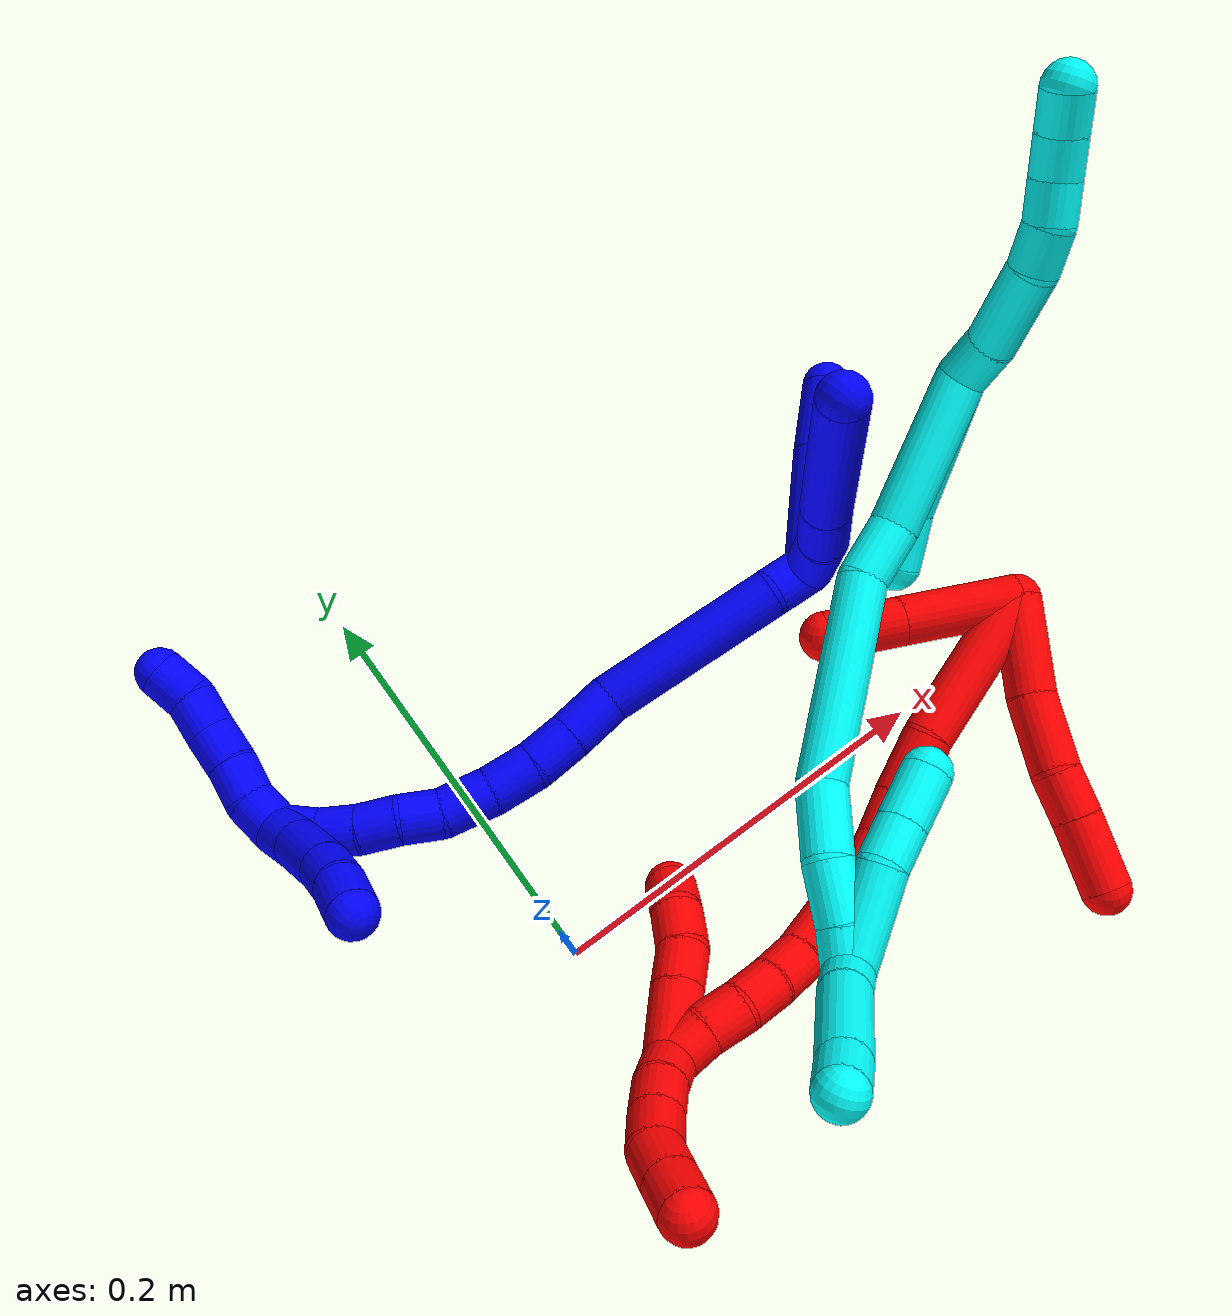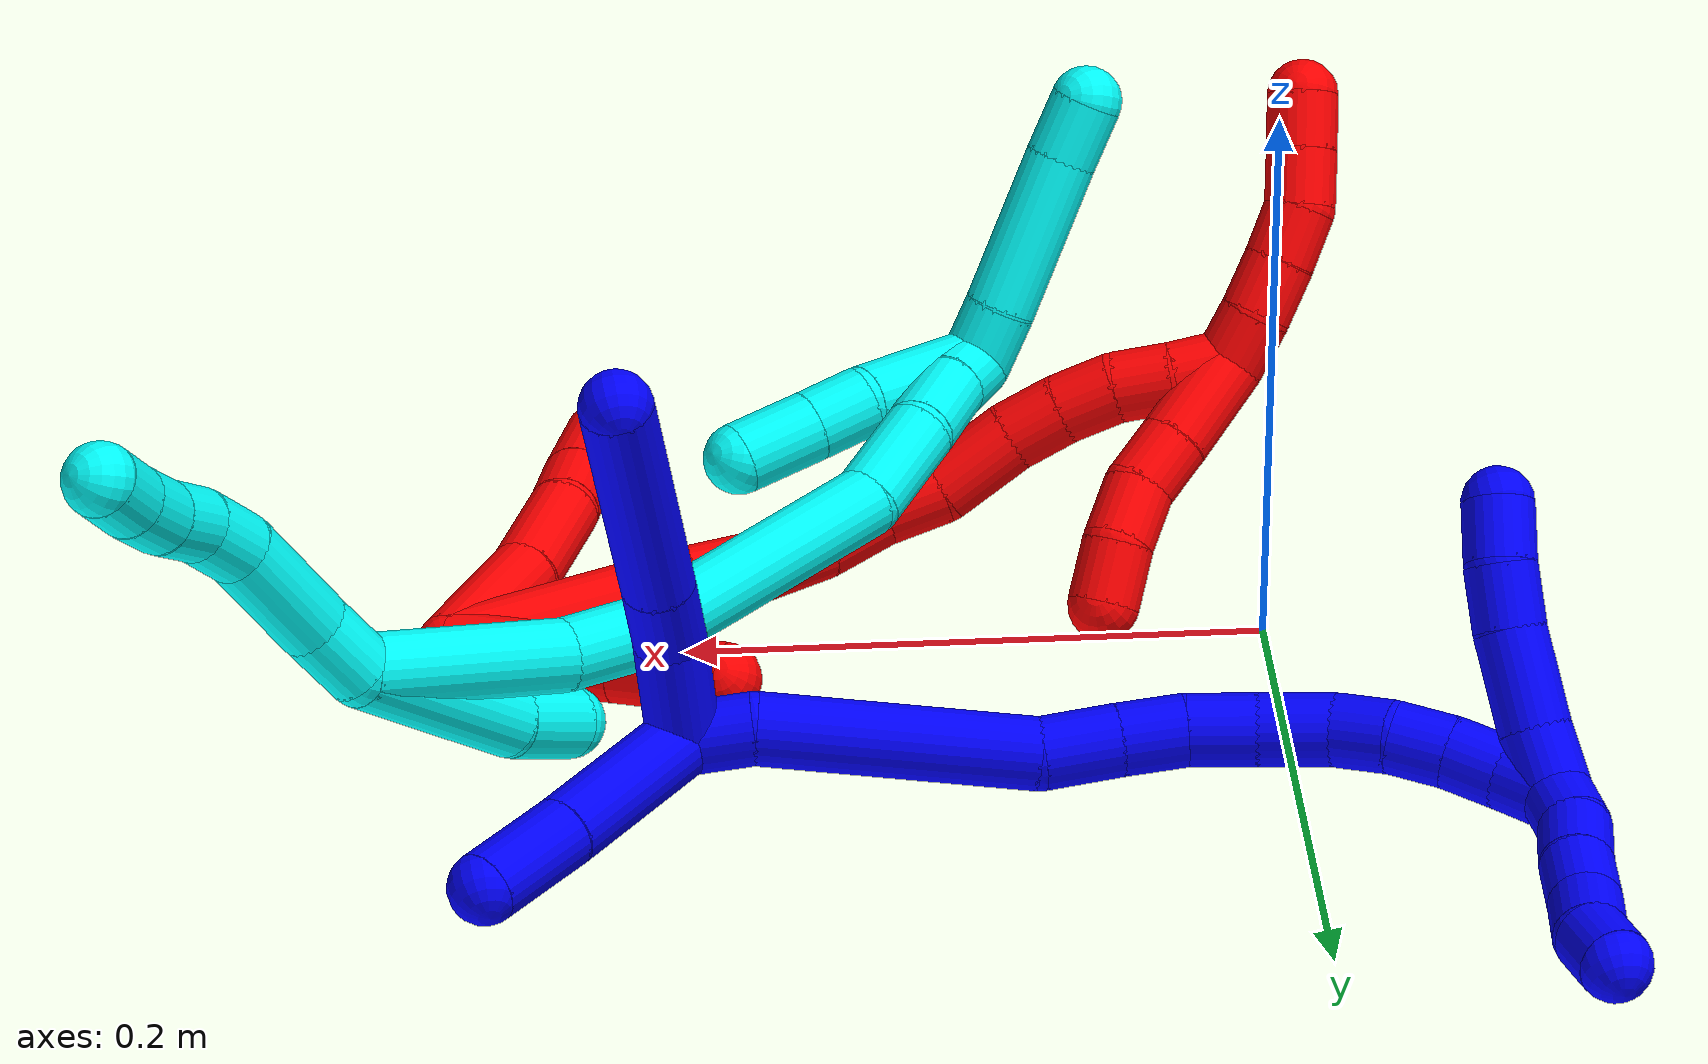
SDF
<sdf version="1.7">
 <world name="default">
  <plugin name="TubeGeneratorPlugin" filename="libtube_generator_plugin.so"/>
  <model name="photoneo_s_sensor">
   <static>1</static>
   <pose>0 0 2 1.57079 1.57079 3.14159</pose>
   <link name="link">
    <inertial><mass>0.1</mass></inertial>
    <sensor name="sensor" type="depth">
     <update_rate>30</update_rate>
     <camera>
      <horizontal_fov>1.22</horizontal_fov>
      <image><width>1920</width><height>1200</height><format>B8G8R8</format></image>
      <clip><near>0.1</near><far>4</far></clip>
      <depth_camera><output>points</output></depth_camera>
     </camera>
     <plugin name="camera_plugin" filename="libgazebo_ros_depth_camera.so">
      <baseline>0.2</baseline>
      <alwaysOn>1</alwaysOn>
      <updateRate>0.0</updateRate>
      <cameraName>camera_ir</cameraName>
      <imageTopicName>/camera/color/image_raw</imageTopicName>
      <cameraInfoTopicName>/camera/color/camera_info</cameraInfoTopicName>
      <depthImageTopicName>/camera/depth/image_raw</depthImageTopicName>
      <depthImageCameraInfoTopicName>/camera/depth/camera_info</depthImageCameraInfoTopicName>
      <pointCloudTopicName>/camera/depth/points</pointCloudTopicName>
      <frameName>fr_optical</frameName>
      <pointCloudCutoff>0.1</pointCloudCutoff>
      <pointCloudCutoffMax>2.0</pointCloudCutoffMax>
      <distortionK1>0</distortionK1>
      <distortionK2>0</distortionK2>
      <distortionK3>0</distortionK3>
      <distortionT1>0</distortionT1>
      <distortionT2>0</distortionT2>
      <CxPrime>0</CxPrime>
      <Cx>0</Cx>
      <Cy>0</Cy>
      <focalLength>0</focalLength>
      <hackBaseline>0</hackBaseline>
     </plugin>
    </sensor>
   </link>
  </model>
  <gravity>0 0 -9.8</gravity>
  <magnetic_field>6e-06 2.3e-05 -4.2e-05</magnetic_field>
  <atmosphere type="adiabatic"/>
  <physics name="default_physics" default="0" type="ode">
   <max_step_size>0.003</max_step_size>
   <real_time_factor>1</real_time_factor>
   <real_time_update_rate>1000</real_time_update_rate>
   <max_contacts>10000</max_contacts>
   <ode>
    <solver>
     <type>quick</type>
     <iters>100</iters>
     <sor>1.3</sor>
     <use_dynamic_moi_rescaling>0</use_dynamic_moi_rescaling>
    </solver>
    <constraints>
     <contact_max_correcting_vel>0</contact_max_correcting_vel>
     <contact_surface_layer>0.001</contact_surface_layer>
     <cfm>0</cfm>
     <erp>0.2</erp>
    </constraints>
   </ode>
  </physics>
  <scene><ambient>0.4 0.4 0.4 1</ambient><background>0.7 0.7 0.7 1</background><shadows>0</shadows></scene>
  <audio><device>default</device></audio>
  <spherical_coordinates>
   <surface_model>EARTH_WGS84</surface_model>
   <latitude_deg>0</latitude_deg>
   <longitude_deg>0</longitude_deg>
   <elevation>0</elevation>
   <heading_deg>0</heading_deg>
  </spherical_coordinates>
  <model name="bin">
   <static>1</static>
   <link name="bottom">
    <collision name="collision-bottom">
     <pose>0 0 -0.01 0 -0 0</pose>
     <geometry><box><size>0.8 0.6 0.02</size></box></geometry>
     <surface>
      <friction><ode><mu>100</mu><mu2>100</mu2></ode></friction>
      <contact><collide_bitmask>65535</collide_bitmask></contact>
     </surface>
    </collision>
   </link>
   <link name="west_wall">
    <collision name="collision-west_wall">
     <pose>-0.41 0 0.1 0 -0 0</pose>
     <geometry><box><size>0.02 0.6 0.2</size></box></geometry>
     <surface>
      <friction><ode><mu>100</mu><mu2>100</mu2></ode></friction>
      <contact><collide_bitmask>65535</collide_bitmask></contact>
     </surface>
    </collision>
   </link>
   <link name="east_wall">
    <collision name="collision-east_wall">
     <pose>0.41 0 0.1 0 -0 0</pose>
     <geometry><box><size>0.02 0.6 0.2</size></box></geometry>
     <surface>
      <friction><ode><mu>100</mu><mu2>100</mu2></ode></friction>
      <contact><collide_bitmask>65535</collide_bitmask></contact>
     </surface>
    </collision>
   </link>
   <link name="south_wall">
    <collision name="collision-south_wall">
     <pose>0 -0.31 0.1 0 -0 0</pose>
     <geometry><box><size>0.8 0.02 0.2</size></box></geometry>
     <surface>
      <friction><ode><mu>100</mu><mu2>100</mu2></ode></friction>
      <contact><collide_bitmask>65535</collide_bitmask></contact>
     </surface>
    </collision>
   </link>
   <link name="north_wall">
    <collision name="collision-north_wall">
     <pose>0 0.31 0.1 0 -0 0</pose>
     <geometry><box><size>0.8 0.02 0.2</size></box></geometry>
     <surface>
      <friction><ode><mu>100</mu><mu2>100</mu2></ode></friction>
      <contact><collide_bitmask>65535</collide_bitmask></contact>
     </surface>
    </collision>
   </link>
  </model>
  <model name="1">
   <static>0</static>
   <link name="1">
    <collision name="collision-cylinder-e_1_2_8">
     <pose>0.000843 -0.018635 -0.007233 1.94104 0.042157 0.061574</pose>
     <geometry><cylinder><radius>0.0125</radius><length>0.040015</length></cylinder></geometry>
     <surface>
      <friction><ode><mu>1.16</mu><mu2>1.16</mu2><slip1>0</slip1><slip2>0</slip2></ode></friction>
      <contact><ode><kp>1e+06</kp><kd>1</kd><max_vel>0</max_vel><min_depth>0.001</min_depth></ode></contact>
     </surface>
    </collision>
    <visual name="visual-cylinder-e_1_2_8">
     <pose>0.000843 -0.018635 -0.007233 1.94104 0.042157 0.061574</pose>
     <geometry><cylinder><radius>0.0125</radius><length>0.040015</length></cylinder></geometry>
     <material><ambient>0 0 1 1</ambient></material>
    </visual>
    <collision name="collision-cylinder-e_2_8_9">
     <pose>0.003111 -0.050708 -0.016261 1.70355 0.10472 0.119601</pose>
     <geometry><cylinder><radius>0.0125</radius><length>0.027263</length></cylinder></geometry>
     <surface>
      <friction><ode><mu>1.16</mu><mu2>1.16</mu2><slip1>0</slip1><slip2>0</slip2></ode></friction>
      <contact><ode><kp>1e+06</kp><kd>1</kd><max_vel>0</max_vel><min_depth>0.001</min_depth></ode></contact>
     </surface>
    </collision>
    <visual name="visual-cylinder-e_2_8_9">
     <pose>0.003111 -0.050708 -0.016261 1.70355 0.10472 0.119601</pose>
     <geometry><cylinder><radius>0.0125</radius><length>0.027263</length></cylinder></geometry>
     <material><ambient>0 0 1 1</ambient></material>
    </visual>
    <collision name="collision-cylinder-e_3_9_6">
     <pose>0.009436 -0.104678 -0.024676 1.73271 0.118734 0.139639</pose>
     <geometry><cylinder><radius>0.0125</radius><length>0.082721</length></cylinder></geometry>
     <surface>
      <friction><ode><mu>1.16</mu><mu2>1.16</mu2><slip1>0</slip1><slip2>0</slip2></ode></friction>
      <contact><ode><kp>1e+06</kp><kd>1</kd><max_vel>0</max_vel><min_depth>0.001</min_depth></ode></contact>
     </surface>
    </collision>
    <visual name="visual-cylinder-e_3_9_6">
     <pose>0.009436 -0.104678 -0.024676 1.73271 0.118734 0.139639</pose>
     <geometry><cylinder><radius>0.0125</radius><length>0.082721</length></cylinder></geometry>
     <material><ambient>0 0 1 1</ambient></material>
    </visual>
    <collision name="collision-cylinder-e_1_2_10">
     <pose>0.023205 -0.007101 0.019633 0.34706 0.838148 0.155857</pose>
     <geometry><cylinder><radius>0.0125</radius><length>0.062429</length></cylinder></geometry>
     <surface>
      <friction><ode><mu>1.16</mu><mu2>1.16</mu2><slip1>0</slip1><slip2>0</slip2></ode></friction>
      <contact><ode><kp>1e+06</kp><kd>1</kd><max_vel>0</max_vel><min_depth>0.001</min_depth></ode></contact>
     </surface>
    </collision>
    <visual name="visual-cylinder-e_1_2_10">
     <pose>0.023205 -0.007101 0.019633 0.34706 0.838148 0.155857</pose>
     <geometry><cylinder><radius>0.0125</radius><length>0.062429</length></cylinder></geometry>
     <material><ambient>0 0 1 1</ambient></material>
    </visual>
    <collision name="collision-cylinder-e_2_10_5">
     <pose>0.06099 -0.018219 0.050409 0.345955 0.888512 0.165951</pose>
     <geometry><cylinder><radius>0.0125</radius><length>0.037571</length></cylinder></geometry>
     <surface>
      <friction><ode><mu>1.16</mu><mu2>1.16</mu2><slip1>0</slip1><slip2>0</slip2></ode></friction>
      <contact><ode><kp>1e+06</kp><kd>1</kd><max_vel>0</max_vel><min_depth>0.001</min_depth></ode></contact>
     </surface>
    </collision>
    <visual name="visual-cylinder-e_2_10_5">
     <pose>0.06099 -0.018219 0.050409 0.345955 0.888512 0.165951</pose>
     <geometry><cylinder><radius>0.0125</radius><length>0.037571</length></cylinder></geometry>
     <material><ambient>0 0 1 1</ambient></material>
    </visual>
    <collision name="collision-cylinder-e_1_2_11">
     <pose>-0.011835 -0.001427 0.001003 0.958294 -1.42445 -0.843315</pose>
     <geometry><cylinder><radius>0.0125</radius><length>0.023926</length></cylinder></geometry>
     <surface>
      <friction><ode><mu>1.16</mu><mu2>1.16</mu2><slip1>0</slip1><slip2>0</slip2></ode></friction>
      <contact><ode><kp>1e+06</kp><kd>1</kd><max_vel>0</max_vel><min_depth>0.001</min_depth></ode></contact>
     </surface>
    </collision>
    <visual name="visual-cylinder-e_1_2_11">
     <pose>-0.011835 -0.001427 0.001003 0.958294 -1.42445 -0.843315</pose>
     <geometry><cylinder><radius>0.0125</radius><length>0.023926</length></cylinder></geometry>
     <material><ambient>0 0 1 1</ambient></material>
    </visual>
    <collision name="collision-cylinder-e_2_11_12">
     <pose>-0.070073 0.002141 0.012131 -0.458359 -1.33213 0.362625</pose>
     <geometry><cylinder><radius>0.0125</radius><length>0.095514</length></cylinder></geometry>
     <surface>
      <friction><ode><mu>1.16</mu><mu2>1.16</mu2><slip1>0</slip1><slip2>0</slip2></ode></friction>
      <contact><ode><kp>1e+06</kp><kd>1</kd><max_vel>0</max_vel><min_depth>0.001</min_depth></ode></contact>
     </surface>
    </collision>
    <visual name="visual-cylinder-e_2_11_12">
     <pose>-0.070073 0.002141 0.012131 -0.458359 -1.33213 0.362625</pose>
     <geometry><cylinder><radius>0.0125</radius><length>0.095514</length></cylinder></geometry>
     <material><ambient>0 0 1 1</ambient></material>
    </visual>
    <collision name="collision-cylinder-e_3_12_13">
     <pose>-0.130024 0.007223 0.021778 -2.96188 -1.53498 2.95536</pose>
     <geometry><cylinder><radius>0.0125</radius><length>0.027113</length></cylinder></geometry>
     <surface>
      <friction><ode><mu>1.16</mu><mu2>1.16</mu2><slip1>0</slip1><slip2>0</slip2></ode></friction>
      <contact><ode><kp>1e+06</kp><kd>1</kd><max_vel>0</max_vel><min_depth>0.001</min_depth></ode></contact>
     </surface>
    </collision>
    <visual name="visual-cylinder-e_3_12_13">
     <pose>-0.130024 0.007223 0.021778 -2.96188 -1.53498 2.95536</pose>
     <geometry><cylinder><radius>0.0125</radius><length>0.027113</length></cylinder></geometry>
     <material><ambient>0 0 1 1</ambient></material>
    </visual>
    <collision name="collision-cylinder-e_4_13_14">
     <pose>-0.154961 0.007085 0.021463 0.943408 -1.54643 -0.92382</pose>
     <geometry><cylinder><radius>0.0125</radius><length>0.022784</length></cylinder></geometry>
     <surface>
      <friction><ode><mu>1.16</mu><mu2>1.16</mu2><slip1>0</slip1><slip2>0</slip2></ode></friction>
      <contact><ode><kp>1e+06</kp><kd>1</kd><max_vel>0</max_vel><min_depth>0.001</min_depth></ode></contact>
     </surface>
    </collision>
    <visual name="visual-cylinder-e_4_13_14">
     <pose>-0.154961 0.007085 0.021463 0.943408 -1.54643 -0.92382</pose>
     <geometry><cylinder><radius>0.0125</radius><length>0.022784</length></cylinder></geometry>
     <material><ambient>0 0 1 1</ambient></material>
    </visual>
    <collision name="collision-cylinder-e_5_14_15">
     <pose>-0.178228 0.006655 0.023856 0.092076 -1.38448 -0.076358</pose>
     <geometry><cylinder><radius>0.0125</radius><length>0.024175</length></cylinder></geometry>
     <surface>
      <friction><ode><mu>1.16</mu><mu2>1.16</mu2><slip1>0</slip1><slip2>0</slip2></ode></friction>
      <contact><ode><kp>1e+06</kp><kd>1</kd><max_vel>0</max_vel><min_depth>0.001</min_depth></ode></contact>
     </surface>
    </collision>
    <visual name="visual-cylinder-e_5_14_15">
     <pose>-0.178228 0.006655 0.023856 0.092076 -1.38448 -0.076358</pose>
     <geometry><cylinder><radius>0.0125</radius><length>0.024175</length></cylinder></geometry>
     <material><ambient>0 0 1 1</ambient></material>
    </visual>
    <collision name="collision-cylinder-e_6_15_16">
     <pose>-0.20252 0.004928 0.029423 0.427586 -1.2835 -0.321676</pose>
     <geometry><cylinder><radius>0.0125</radius><length>0.025888</length></cylinder></geometry>
     <surface>
      <friction><ode><mu>1.16</mu><mu2>1.16</mu2><slip1>0</slip1><slip2>0</slip2></ode></friction>
      <contact><ode><kp>1e+06</kp><kd>1</kd><max_vel>0</max_vel><min_depth>0.001</min_depth></ode></contact>
     </surface>
    </collision>
    <visual name="visual-cylinder-e_6_15_16">
     <pose>-0.20252 0.004928 0.029423 0.427586 -1.2835 -0.321676</pose>
     <geometry><cylinder><radius>0.0125</radius><length>0.025888</length></cylinder></geometry>
     <material><ambient>0 0 1 1</ambient></material>
    </visual>
    <collision name="collision-cylinder-e_7_16_17">
     <pose>-0.223501 0.000851 0.037608 0.485195 -1.00175 -0.269312</pose>
     <geometry><cylinder><radius>0.0125</radius><length>0.020341</length></cylinder></geometry>
     <surface>
      <friction><ode><mu>1.16</mu><mu2>1.16</mu2><slip1>0</slip1><slip2>0</slip2></ode></friction>
      <contact><ode><kp>1e+06</kp><kd>1</kd><max_vel>0</max_vel><min_depth>0.001</min_depth></ode></contact>
     </surface>
    </collision>
    <visual name="visual-cylinder-e_7_16_17">
     <pose>-0.223501 0.000851 0.037608 0.485195 -1.00175 -0.269312</pose>
     <geometry><cylinder><radius>0.0125</radius><length>0.020341</length></cylinder></geometry>
     <material><ambient>0 0 1 1</ambient></material>
    </visual>
    <collision name="collision-cylinder-e_8_17_18">
     <pose>-0.240782 -0.002171 0.047505 0.092106 -1.04373 -0.052989</pose>
     <geometry><cylinder><radius>0.0125</radius><length>0.020161</length></cylinder></geometry>
     <surface>
      <friction><ode><mu>1.16</mu><mu2>1.16</mu2><slip1>0</slip1><slip2>0</slip2></ode></friction>
      <contact><ode><kp>1e+06</kp><kd>1</kd><max_vel>0</max_vel><min_depth>0.001</min_depth></ode></contact>
     </surface>
    </collision>
    <visual name="visual-cylinder-e_8_17_18">
     <pose>-0.240782 -0.002171 0.047505 0.092106 -1.04373 -0.052989</pose>
     <geometry><cylinder><radius>0.0125</radius><length>0.020161</length></cylinder></geometry>
     <material><ambient>0 0 1 1</ambient></material>
    </visual>
    <collision name="collision-cylinder-e_9_18_19">
     <pose>-0.257344 -0.003239 0.058762 0.096572 -0.899383 -0.046641</pose>
     <geometry><cylinder><radius>0.0125</radius><length>0.020052</length></cylinder></geometry>
     <surface>
      <friction><ode><mu>1.16</mu><mu2>1.16</mu2><slip1>0</slip1><slip2>0</slip2></ode></friction>
      <contact><ode><kp>1e+06</kp><kd>1</kd><max_vel>0</max_vel><min_depth>0.001</min_depth></ode></contact>
     </surface>
    </collision>
    <visual name="visual-cylinder-e_9_18_19">
     <pose>-0.257344 -0.003239 0.058762 0.096572 -0.899383 -0.046641</pose>
     <geometry><cylinder><radius>0.0125</radius><length>0.020052</length></cylinder></geometry>
     <material><ambient>0 0 1 1</ambient></material>
    </visual>
    <collision name="collision-cylinder-e_10_19_1">
     <pose>-0.27192 -0.006137 0.072037 0.314252 -0.735678 -0.121961</pose>
     <geometry><cylinder><radius>0.0125</radius><length>0.020046</length></cylinder></geometry>
     <surface>
      <friction><ode><mu>1.16</mu><mu2>1.16</mu2><slip1>0</slip1><slip2>0</slip2></ode></friction>
      <contact><ode><kp>1e+06</kp><kd>1</kd><max_vel>0</max_vel><min_depth>0.001</min_depth></ode></contact>
     </surface>
    </collision>
    <visual name="visual-cylinder-e_10_19_1">
     <pose>-0.27192 -0.006137 0.072037 0.314252 -0.735678 -0.121961</pose>
     <geometry><cylinder><radius>0.0125</radius><length>0.020046</length></cylinder></geometry>
     <material><ambient>0 0 1 1</ambient></material>
    </visual>
    <collision name="collision-cylinder-e_1_1_20">
     <pose>-0.277113 -0.01292 0.068894 2.72758 0.136588 0.629718</pose>
     <geometry><cylinder><radius>0.0125</radius><length>0.022513</length></cylinder></geometry>
     <surface>
      <friction><ode><mu>1.16</mu><mu2>1.16</mu2><slip1>0</slip1><slip2>0</slip2></ode></friction>
      <contact><ode><kp>1e+06</kp><kd>1</kd><max_vel>0</max_vel><min_depth>0.001</min_depth></ode></contact>
     </surface>
    </collision>
    <visual name="visual-cylinder-e_1_1_20">
     <pose>-0.277113 -0.01292 0.068894 2.72758 0.136588 0.629718</pose>
     <geometry><cylinder><radius>0.0125</radius><length>0.022513</length></cylinder></geometry>
     <material><ambient>0 0 1 1</ambient></material>
    </visual>
    <collision name="collision-cylinder-e_2_20_21">
     <pose>-0.274212 -0.02554 0.043804 2.64139 0.080502 0.312732</pose>
     <geometry><cylinder><radius>0.0125</radius><length>0.034027</length></cylinder></geometry>
     <surface>
      <friction><ode><mu>1.16</mu><mu2>1.16</mu2><slip1>0</slip1><slip2>0</slip2></ode></friction>
      <contact><ode><kp>1e+06</kp><kd>1</kd><max_vel>0</max_vel><min_depth>0.001</min_depth></ode></contact>
     </surface>
    </collision>
    <visual name="visual-cylinder-e_2_20_21">
     <pose>-0.274212 -0.02554 0.043804 2.64139 0.080502 0.312732</pose>
     <geometry><cylinder><radius>0.0125</radius><length>0.034027</length></cylinder></geometry>
     <material><ambient>0 0 1 1</ambient></material>
    </visual>
    <collision name="collision-cylinder-e_3_21_22">
     <pose>-0.273079 -0.039201 0.019377 2.61664 -0.021267 -0.079118</pose>
     <geometry><cylinder><radius>0.0125</radius><length>0.022067</length></cylinder></geometry>
     <surface>
      <friction><ode><mu>1.16</mu><mu2>1.16</mu2><slip1>0</slip1><slip2>0</slip2></ode></friction>
      <contact><ode><kp>1e+06</kp><kd>1</kd><max_vel>0</max_vel><min_depth>0.001</min_depth></ode></contact>
     </surface>
    </collision>
    <visual name="visual-cylinder-e_3_21_22">
     <pose>-0.273079 -0.039201 0.019377 2.61664 -0.021267 -0.079118</pose>
     <geometry><cylinder><radius>0.0125</radius><length>0.022067</length></cylinder></geometry>
     <material><ambient>0 0 1 1</ambient></material>
    </visual>
    <collision name="collision-cylinder-e_4_22_4">
     <pose>-0.27491 -0.048619 -4e-06 2.76501 -0.149775 -0.750207</pose>
     <geometry><cylinder><radius>0.0125</radius><length>0.021393</length></cylinder></geometry>
     <surface>
      <friction><ode><mu>1.16</mu><mu2>1.16</mu2><slip1>0</slip1><slip2>0</slip2></ode></friction>
      <contact><ode><kp>1e+06</kp><kd>1</kd><max_vel>0</max_vel><min_depth>0.001</min_depth></ode></contact>
     </surface>
    </collision>
    <visual name="visual-cylinder-e_4_22_4">
     <pose>-0.27491 -0.048619 -4e-06 2.76501 -0.149775 -0.750207</pose>
     <geometry><cylinder><radius>0.0125</radius><length>0.021393</length></cylinder></geometry>
     <material><ambient>0 0 1 1</ambient></material>
    </visual>
    <collision name="collision-cylinder-e_1_1_23">
     <pose>-0.279172 -0.012144 0.088375 0.380685 -0.052654 -0.010147</pose>
     <geometry><cylinder><radius>0.0125</radius><length>0.02</length></cylinder></geometry>
     <surface>
      <friction><ode><mu>1.16</mu><mu2>1.16</mu2><slip1>0</slip1><slip2>0</slip2></ode></friction>
      <contact><ode><kp>1e+06</kp><kd>1</kd><max_vel>0</max_vel><min_depth>0.001</min_depth></ode></contact>
     </surface>
    </collision>
    <visual name="visual-cylinder-e_1_1_23">
     <pose>-0.279172 -0.012144 0.088375 0.380685 -0.052654 -0.010147</pose>
     <geometry><cylinder><radius>0.0125</radius><length>0.02</length></cylinder></geometry>
     <material><ambient>0 0 1 1</ambient></material>
    </visual>
    <collision name="collision-cylinder-e_2_23_24">
     <pose>-0.277473 -0.019207 0.106801 0.350977 0.224424 0.039956</pose>
     <geometry><cylinder><radius>0.0125</radius><length>0.02</length></cylinder></geometry>
     <surface>
      <friction><ode><mu>1.16</mu><mu2>1.16</mu2><slip1>0</slip1><slip2>0</slip2></ode></friction>
      <contact><ode><kp>1e+06</kp><kd>1</kd><max_vel>0</max_vel><min_depth>0.001</min_depth></ode></contact>
     </surface>
    </collision>
    <visual name="visual-cylinder-e_2_23_24">
     <pose>-0.277473 -0.019207 0.106801 0.350977 0.224424 0.039956</pose>
     <geometry><cylinder><radius>0.0125</radius><length>0.02</length></cylinder></geometry>
     <material><ambient>0 0 1 1</ambient></material>
    </visual>
    <collision name="collision-cylinder-e_3_24_25">
     <pose>-0.27413 -0.025543 0.125434 0.305043 0.112044 0.017241</pose>
     <geometry><cylinder><radius>0.0125</radius><length>0.02</length></cylinder></geometry>
     <surface>
      <friction><ode><mu>1.16</mu><mu2>1.16</mu2><slip1>0</slip1><slip2>0</slip2></ode></friction>
      <contact><ode><kp>1e+06</kp><kd>1</kd><max_vel>0</max_vel><min_depth>0.001</min_depth></ode></contact>
     </surface>
    </collision>
    <visual name="visual-cylinder-e_3_24_25">
     <pose>-0.27413 -0.025543 0.125434 0.305043 0.112044 0.017241</pose>
     <geometry><cylinder><radius>0.0125</radius><length>0.02</length></cylinder></geometry>
     <material><ambient>0 0 1 1</ambient></material>
    </visual>
    <collision name="collision-cylinder-e_4_25_26">
     <pose>-0.271341 -0.032792 0.143802 0.447272 0.167862 0.038264</pose>
     <geometry><cylinder><radius>0.0125</radius><length>0.02</length></cylinder></geometry>
     <surface>
      <friction><ode><mu>1.16</mu><mu2>1.16</mu2><slip1>0</slip1><slip2>0</slip2></ode></friction>
      <contact><ode><kp>1e+06</kp><kd>1</kd><max_vel>0</max_vel><min_depth>0.001</min_depth></ode></contact>
     </surface>
    </collision>
    <visual name="visual-cylinder-e_4_25_26">
     <pose>-0.271341 -0.032792 0.143802 0.447272 0.167862 0.038264</pose>
     <geometry><cylinder><radius>0.0125</radius><length>0.02</length></cylinder></geometry>
     <material><ambient>0 0 1 1</ambient></material>
    </visual>
    <collision name="collision-cylinder-e_5_26_3">
     <pose>-0.271235 -0.041574 0.161475 0.475132 -0.157103 -0.038115</pose>
     <geometry><cylinder><radius>0.0125</radius><length>0.02</length></cylinder></geometry>
     <surface>
      <friction><ode><mu>1.16</mu><mu2>1.16</mu2><slip1>0</slip1><slip2>0</slip2></ode></friction>
      <contact><ode><kp>1e+06</kp><kd>1</kd><max_vel>0</max_vel><min_depth>0.001</min_depth></ode></contact>
     </surface>
    </collision>
    <visual name="visual-cylinder-e_5_26_3">
     <pose>-0.271235 -0.041574 0.161475 0.475132 -0.157103 -0.038115</pose>
     <geometry><cylinder><radius>0.0125</radius><length>0.02</length></cylinder></geometry>
     <material><ambient>0 0 1 1</ambient></material>
    </visual>
    <collision name="collision-sphere-3">
     <pose>-0.272799 -0.046093 0.170258 0 -0 0</pose>
     <geometry><sphere><radius>0.0125</radius></sphere></geometry>
     <surface>
      <friction><ode><mu>1.16</mu><mu2>1.16</mu2><slip1>0</slip1><slip2>0</slip2></ode></friction>
      <contact><ode><kp>1e+06</kp><kd>1</kd><max_vel>0</max_vel><min_depth>0.001</min_depth></ode></contact>
     </surface>
    </collision>
    <visual name="visual-sphere-3">
     <pose>-0.272799 -0.046093 0.170258 0 -0 0</pose>
     <geometry><sphere><radius>0.0125</radius></sphere></geometry>
     <material><ambient>0 0 1 1</ambient></material>
    </visual>
    <collision name="collision-sphere-26">
     <pose>-0.26967 -0.037056 0.152692 0 -0 0</pose>
     <geometry><sphere><radius>0.0125</radius></sphere></geometry>
     <surface>
      <friction><ode><mu>1.16</mu><mu2>1.16</mu2><slip1>0</slip1><slip2>0</slip2></ode></friction>
      <contact><ode><kp>1e+06</kp><kd>1</kd><max_vel>0</max_vel><min_depth>0.001</min_depth></ode></contact>
     </surface>
    </collision>
    <visual name="visual-sphere-26">
     <pose>-0.26967 -0.037056 0.152692 0 -0 0</pose>
     <geometry><sphere><radius>0.0125</radius></sphere></geometry>
     <material><ambient>0 0 1 1</ambient></material>
    </visual>
    <collision name="collision-sphere-25">
     <pose>-0.273011 -0.028528 0.134913 0 -0 0</pose>
     <geometry><sphere><radius>0.0125</radius></sphere></geometry>
     <surface>
      <friction><ode><mu>1.16</mu><mu2>1.16</mu2><slip1>0</slip1><slip2>0</slip2></ode></friction>
      <contact><ode><kp>1e+06</kp><kd>1</kd><max_vel>0</max_vel><min_depth>0.001</min_depth></ode></contact>
     </surface>
    </collision>
    <visual name="visual-sphere-25">
     <pose>-0.273011 -0.028528 0.134913 0 -0 0</pose>
     <geometry><sphere><radius>0.0125</radius></sphere></geometry>
     <material><ambient>0 0 1 1</ambient></material>
    </visual>
    <collision name="collision-sphere-24">
     <pose>-0.275248 -0.022559 0.115956 0 -0 0</pose>
     <geometry><sphere><radius>0.0125</radius></sphere></geometry>
     <surface>
      <friction><ode><mu>1.16</mu><mu2>1.16</mu2><slip1>0</slip1><slip2>0</slip2></ode></friction>
      <contact><ode><kp>1e+06</kp><kd>1</kd><max_vel>0</max_vel><min_depth>0.001</min_depth></ode></contact>
     </surface>
    </collision>
    <visual name="visual-sphere-24">
     <pose>-0.275248 -0.022559 0.115956 0 -0 0</pose>
     <geometry><sphere><radius>0.0125</radius></sphere></geometry>
     <material><ambient>0 0 1 1</ambient></material>
    </visual>
    <collision name="collision-sphere-23">
     <pose>-0.279699 -0.015855 0.097646 0 -0 0</pose>
     <geometry><sphere><radius>0.0125</radius></sphere></geometry>
     <surface>
      <friction><ode><mu>1.16</mu><mu2>1.16</mu2><slip1>0</slip1><slip2>0</slip2></ode></friction>
      <contact><ode><kp>1e+06</kp><kd>1</kd><max_vel>0</max_vel><min_depth>0.001</min_depth></ode></contact>
     </surface>
    </collision>
    <visual name="visual-sphere-23">
     <pose>-0.279699 -0.015855 0.097646 0 -0 0</pose>
     <geometry><sphere><radius>0.0125</radius></sphere></geometry>
     <material><ambient>0 0 1 1</ambient></material>
    </visual>
    <collision name="collision-sphere-4">
     <pose>-0.276506 -0.052509 -0.009839 0 -0 0</pose>
     <geometry><sphere><radius>0.0125</radius></sphere></geometry>
     <surface>
      <friction><ode><mu>1.16</mu><mu2>1.16</mu2><slip1>0</slip1><slip2>0</slip2></ode></friction>
      <contact><ode><kp>1e+06</kp><kd>1</kd><max_vel>0</max_vel><min_depth>0.001</min_depth></ode></contact>
     </surface>
    </collision>
    <visual name="visual-sphere-4">
     <pose>-0.276506 -0.052509 -0.009839 0 -0 0</pose>
     <geometry><sphere><radius>0.0125</radius></sphere></geometry>
     <material><ambient>0 0 1 1</ambient></material>
    </visual>
    <collision name="collision-sphere-22">
     <pose>-0.273313 -0.04473 0.009832 0 -0 0</pose>
     <geometry><sphere><radius>0.0125</radius></sphere></geometry>
     <surface>
      <friction><ode><mu>1.16</mu><mu2>1.16</mu2><slip1>0</slip1><slip2>0</slip2></ode></friction>
      <contact><ode><kp>1e+06</kp><kd>1</kd><max_vel>0</max_vel><min_depth>0.001</min_depth></ode></contact>
     </surface>
    </collision>
    <visual name="visual-sphere-22">
     <pose>-0.273313 -0.04473 0.009832 0 -0 0</pose>
     <geometry><sphere><radius>0.0125</radius></sphere></geometry>
     <material><ambient>0 0 1 1</ambient></material>
    </visual>
    <collision name="collision-sphere-21">
     <pose>-0.272844 -0.033673 0.028923 0 -0 0</pose>
     <geometry><sphere><radius>0.0125</radius></sphere></geometry>
     <surface>
      <friction><ode><mu>1.16</mu><mu2>1.16</mu2><slip1>0</slip1><slip2>0</slip2></ode></friction>
      <contact><ode><kp>1e+06</kp><kd>1</kd><max_vel>0</max_vel><min_depth>0.001</min_depth></ode></contact>
     </surface>
    </collision>
    <visual name="visual-sphere-21">
     <pose>-0.272844 -0.033673 0.028923 0 -0 0</pose>
     <geometry><sphere><radius>0.0125</radius></sphere></geometry>
     <material><ambient>0 0 1 1</ambient></material>
    </visual>
    <collision name="collision-sphere-20">
     <pose>-0.27558 -0.017406 0.058684 0 -0 0</pose>
     <geometry><sphere><radius>0.0125</radius></sphere></geometry>
     <surface>
      <friction><ode><mu>1.16</mu><mu2>1.16</mu2><slip1>0</slip1><slip2>0</slip2></ode></friction>
      <contact><ode><kp>1e+06</kp><kd>1</kd><max_vel>0</max_vel><min_depth>0.001</min_depth></ode></contact>
     </surface>
    </collision>
    <visual name="visual-sphere-20">
     <pose>-0.27558 -0.017406 0.058684 0 -0 0</pose>
     <geometry><sphere><radius>0.0125</radius></sphere></geometry>
     <material><ambient>0 0 1 1</ambient></material>
    </visual>
    <collision name="collision-sphere-5">
     <pose>0.07557 -0.022236 0.061553 0 -0 0</pose>
     <geometry><sphere><radius>0.0125</radius></sphere></geometry>
     <surface>
      <friction><ode><mu>1.16</mu><mu2>1.16</mu2><slip1>0</slip1><slip2>0</slip2></ode></friction>
      <contact><ode><kp>1e+06</kp><kd>1</kd><max_vel>0</max_vel><min_depth>0.001</min_depth></ode></contact>
     </surface>
    </collision>
    <visual name="visual-sphere-5">
     <pose>0.07557 -0.022236 0.061553 0 -0 0</pose>
     <geometry><sphere><radius>0.0125</radius></sphere></geometry>
     <material><ambient>0 0 1 1</ambient></material>
    </visual>
    <collision name="collision-sphere-10">
     <pose>0.04641 -0.014202 0.039265 0 -0 0</pose>
     <geometry><sphere><radius>0.0125</radius></sphere></geometry>
     <surface>
      <friction><ode><mu>1.16</mu><mu2>1.16</mu2><slip1>0</slip1><slip2>0</slip2></ode></friction>
      <contact><ode><kp>1e+06</kp><kd>1</kd><max_vel>0</max_vel><min_depth>0.001</min_depth></ode></contact>
     </surface>
    </collision>
    <visual name="visual-sphere-10">
     <pose>0.04641 -0.014202 0.039265 0 -0 0</pose>
     <geometry><sphere><radius>0.0125</radius></sphere></geometry>
     <material><ambient>0 0 1 1</ambient></material>
    </visual>
    <collision name="collision-sphere-6">
     <pose>0.014335 -0.145211 -0.031297 0 -0 0</pose>
     <geometry><sphere><radius>0.0125</radius></sphere></geometry>
     <surface>
      <friction><ode><mu>1.16</mu><mu2>1.16</mu2><slip1>0</slip1><slip2>0</slip2></ode></friction>
      <contact><ode><kp>1e+06</kp><kd>1</kd><max_vel>0</max_vel><min_depth>0.001</min_depth></ode></contact>
     </surface>
    </collision>
    <visual name="visual-sphere-6">
     <pose>0.014335 -0.145211 -0.031297 0 -0 0</pose>
     <geometry><sphere><radius>0.0125</radius></sphere></geometry>
     <material><ambient>0 0 1 1</ambient></material>
    </visual>
    <collision name="collision-sphere-9">
     <pose>0.004536 -0.064146 -0.018055 0 -0 0</pose>
     <geometry><sphere><radius>0.0125</radius></sphere></geometry>
     <surface>
      <friction><ode><mu>1.16</mu><mu2>1.16</mu2><slip1>0</slip1><slip2>0</slip2></ode></friction>
      <contact><ode><kp>1e+06</kp><kd>1</kd><max_vel>0</max_vel><min_depth>0.001</min_depth></ode></contact>
     </surface>
    </collision>
    <visual name="visual-sphere-9">
     <pose>0.004536 -0.064146 -0.018055 0 -0 0</pose>
     <geometry><sphere><radius>0.0125</radius></sphere></geometry>
     <material><ambient>0 0 1 1</ambient></material>
    </visual>
    <collision name="collision-sphere-2">
     <geometry><sphere><radius>0.0125</radius></sphere></geometry>
     <surface>
      <friction><ode><mu>1.16</mu><mu2>1.16</mu2><slip1>0</slip1><slip2>0</slip2></ode></friction>
      <contact><ode><kp>1e+06</kp><kd>1</kd><max_vel>0</max_vel><min_depth>0.001</min_depth></ode></contact>
     </surface>
    </collision>
    <visual name="visual-sphere-2">
     <geometry><sphere><radius>0.0125</radius></sphere></geometry>
     <material><ambient>0 0 1 1</ambient></material>
    </visual>
    <collision name="collision-sphere-19">
     <pose>-0.265193 -0.00384 0.06497 0 -0 0</pose>
     <geometry><sphere><radius>0.0125</radius></sphere></geometry>
     <surface>
      <friction><ode><mu>1.16</mu><mu2>1.16</mu2><slip1>0</slip1><slip2>0</slip2></ode></friction>
      <contact><ode><kp>1e+06</kp><kd>1</kd><max_vel>0</max_vel><min_depth>0.001</min_depth></ode></contact>
     </surface>
    </collision>
    <visual name="visual-sphere-19">
     <pose>-0.265193 -0.00384 0.06497 0 -0 0</pose>
     <geometry><sphere><radius>0.0125</radius></sphere></geometry>
     <material><ambient>0 0 1 1</ambient></material>
    </visual>
    <collision name="collision-sphere-8">
     <pose>0.001686 -0.037271 -0.014466 0 -0 0</pose>
     <geometry><sphere><radius>0.0125</radius></sphere></geometry>
     <surface>
      <friction><ode><mu>1.16</mu><mu2>1.16</mu2><slip1>0</slip1><slip2>0</slip2></ode></friction>
      <contact><ode><kp>1e+06</kp><kd>1</kd><max_vel>0</max_vel><min_depth>0.001</min_depth></ode></contact>
     </surface>
    </collision>
    <visual name="visual-sphere-8">
     <pose>0.001686 -0.037271 -0.014466 0 -0 0</pose>
     <geometry><sphere><radius>0.0125</radius></sphere></geometry>
     <material><ambient>0 0 1 1</ambient></material>
    </visual>
    <collision name="collision-sphere-11">
     <pose>-0.02367 -0.002855 0.002006 0 -0 0</pose>
     <geometry><sphere><radius>0.0125</radius></sphere></geometry>
     <surface>
      <friction><ode><mu>1.16</mu><mu2>1.16</mu2><slip1>0</slip1><slip2>0</slip2></ode></friction>
      <contact><ode><kp>1e+06</kp><kd>1</kd><max_vel>0</max_vel><min_depth>0.001</min_depth></ode></contact>
     </surface>
    </collision>
    <visual name="visual-sphere-11">
     <pose>-0.02367 -0.002855 0.002006 0 -0 0</pose>
     <geometry><sphere><radius>0.0125</radius></sphere></geometry>
     <material><ambient>0 0 1 1</ambient></material>
    </visual>
    <collision name="collision-sphere-12">
     <pose>-0.116476 0.007137 0.022255 0 -0 0</pose>
     <geometry><sphere><radius>0.0125</radius></sphere></geometry>
     <surface>
      <friction><ode><mu>1.16</mu><mu2>1.16</mu2><slip1>0</slip1><slip2>0</slip2></ode></friction>
      <contact><ode><kp>1e+06</kp><kd>1</kd><max_vel>0</max_vel><min_depth>0.001</min_depth></ode></contact>
     </surface>
    </collision>
    <visual name="visual-sphere-12">
     <pose>-0.116476 0.007137 0.022255 0 -0 0</pose>
     <geometry><sphere><radius>0.0125</radius></sphere></geometry>
     <material><ambient>0 0 1 1</ambient></material>
    </visual>
    <collision name="collision-sphere-13">
     <pose>-0.143572 0.00731 0.0213 0 -0 0</pose>
     <geometry><sphere><radius>0.0125</radius></sphere></geometry>
     <surface>
      <friction><ode><mu>1.16</mu><mu2>1.16</mu2><slip1>0</slip1><slip2>0</slip2></ode></friction>
      <contact><ode><kp>1e+06</kp><kd>1</kd><max_vel>0</max_vel><min_depth>0.001</min_depth></ode></contact>
     </surface>
    </collision>
    <visual name="visual-sphere-13">
     <pose>-0.143572 0.00731 0.0213 0 -0 0</pose>
     <geometry><sphere><radius>0.0125</radius></sphere></geometry>
     <material><ambient>0 0 1 1</ambient></material>
    </visual>
    <collision name="collision-sphere-14">
     <pose>-0.16635 0.006861 0.021626 0 -0 0</pose>
     <geometry><sphere><radius>0.0125</radius></sphere></geometry>
     <surface>
      <friction><ode><mu>1.16</mu><mu2>1.16</mu2><slip1>0</slip1><slip2>0</slip2></ode></friction>
      <contact><ode><kp>1e+06</kp><kd>1</kd><max_vel>0</max_vel><min_depth>0.001</min_depth></ode></contact>
     </surface>
    </collision>
    <visual name="visual-sphere-14">
     <pose>-0.16635 0.006861 0.021626 0 -0 0</pose>
     <geometry><sphere><radius>0.0125</radius></sphere></geometry>
     <material><ambient>0 0 1 1</ambient></material>
    </visual>
    <collision name="collision-sphere-15">
     <pose>-0.190106 0.006449 0.026085 0 -0 0</pose>
     <geometry><sphere><radius>0.0125</radius></sphere></geometry>
     <surface>
      <friction><ode><mu>1.16</mu><mu2>1.16</mu2><slip1>0</slip1><slip2>0</slip2></ode></friction>
      <contact><ode><kp>1e+06</kp><kd>1</kd><max_vel>0</max_vel><min_depth>0.001</min_depth></ode></contact>
     </surface>
    </collision>
    <visual name="visual-sphere-15">
     <pose>-0.190106 0.006449 0.026085 0 -0 0</pose>
     <geometry><sphere><radius>0.0125</radius></sphere></geometry>
     <material><ambient>0 0 1 1</ambient></material>
    </visual>
    <collision name="collision-sphere-16">
     <pose>-0.214934 0.003407 0.032761 0 -0 0</pose>
     <geometry><sphere><radius>0.0125</radius></sphere></geometry>
     <surface>
      <friction><ode><mu>1.16</mu><mu2>1.16</mu2><slip1>0</slip1><slip2>0</slip2></ode></friction>
      <contact><ode><kp>1e+06</kp><kd>1</kd><max_vel>0</max_vel><min_depth>0.001</min_depth></ode></contact>
     </surface>
    </collision>
    <visual name="visual-sphere-16">
     <pose>-0.214934 0.003407 0.032761 0 -0 0</pose>
     <geometry><sphere><radius>0.0125</radius></sphere></geometry>
     <material><ambient>0 0 1 1</ambient></material>
    </visual>
    <collision name="collision-sphere-17">
     <pose>-0.232069 -0.001705 0.042456 0 -0 0</pose>
     <geometry><sphere><radius>0.0125</radius></sphere></geometry>
     <surface>
      <friction><ode><mu>1.16</mu><mu2>1.16</mu2><slip1>0</slip1><slip2>0</slip2></ode></friction>
      <contact><ode><kp>1e+06</kp><kd>1</kd><max_vel>0</max_vel><min_depth>0.001</min_depth></ode></contact>
     </surface>
    </collision>
    <visual name="visual-sphere-17">
     <pose>-0.232069 -0.001705 0.042456 0 -0 0</pose>
     <geometry><sphere><radius>0.0125</radius></sphere></geometry>
     <material><ambient>0 0 1 1</ambient></material>
    </visual>
    <collision name="collision-sphere-18">
     <pose>-0.249494 -0.002637 0.052554 0 -0 0</pose>
     <geometry><sphere><radius>0.0125</radius></sphere></geometry>
     <surface>
      <friction><ode><mu>1.16</mu><mu2>1.16</mu2><slip1>0</slip1><slip2>0</slip2></ode></friction>
      <contact><ode><kp>1e+06</kp><kd>1</kd><max_vel>0</max_vel><min_depth>0.001</min_depth></ode></contact>
     </surface>
    </collision>
    <visual name="visual-sphere-18">
     <pose>-0.249494 -0.002637 0.052554 0 -0 0</pose>
     <geometry><sphere><radius>0.0125</radius></sphere></geometry>
     <material><ambient>0 0 1 1</ambient></material>
    </visual>
    <collision name="collision-sphere-1">
     <pose>-0.278646 -0.008434 0.079104 0 -0 0</pose>
     <geometry><sphere><radius>0.0125</radius></sphere></geometry>
     <surface>
      <friction><ode><mu>1.16</mu><mu2>1.16</mu2><slip1>0</slip1><slip2>0</slip2></ode></friction>
      <contact><ode><kp>1e+06</kp><kd>1</kd><max_vel>0</max_vel><min_depth>0.001</min_depth></ode></contact>
     </surface>
    </collision>
    <visual name="visual-sphere-1">
     <pose>-0.278646 -0.008434 0.079104 0 -0 0</pose>
     <geometry><sphere><radius>0.0125</radius></sphere></geometry>
     <material><ambient>0 0 1 1</ambient></material>
    </visual>
    <inertial>
     <pose>-0.1252 -0.022672 0.032371 0 -0 0</pose>
     <mass>0.75</mass>
     <inertia>
      <ixx>0.000119</ixx>
      <ixy>0</ixy>
      <ixz>0</ixz>
      <iyy>0.000107</iyy>
      <iyz>0</iyz>
      <izz>0.000135</izz>
     </inertia>
    </inertial>
   </link>
   <pose>0.204009 0.083364 0.018875 -1.95536 0.064891 0.100374</pose>
  </model>
  <model name="2">
   <static>0</static>
   <link name="2">
    <collision name="collision-cylinder-e_1_2_8">
     <pose>-0.011837 -0.01509 -0.016659 2.40557 -0.484735 -1.14032</pose>
     <geometry><cylinder><radius>0.0125</radius><length>0.050807</length></cylinder></geometry>
     <surface>
      <friction><ode><mu>1.16</mu><mu2>1.16</mu2><slip1>0</slip1><slip2>0</slip2></ode></friction>
      <contact><ode><kp>1e+06</kp><kd>1</kd><max_vel>0</max_vel><min_depth>0.001</min_depth></ode></contact>
     </surface>
    </collision>
    <visual name="visual-cylinder-e_1_2_8">
     <pose>-0.011837 -0.01509 -0.016659 2.40557 -0.484735 -1.14032</pose>
     <geometry><cylinder><radius>0.0125</radius><length>0.050807</length></cylinder></geometry>
     <material><ambient>1 0 0 1</ambient></material>
    </visual>
    <collision name="collision-cylinder-e_2_8_9">
     <pose>-0.030712 -0.043715 -0.045119 2.28787 -0.373496 -0.787478</pose>
     <geometry><cylinder><radius>0.0125</radius><length>0.038575</length></cylinder></geometry>
     <surface>
      <friction><ode><mu>1.16</mu><mu2>1.16</mu2><slip1>0</slip1><slip2>0</slip2></ode></friction>
      <contact><ode><kp>1e+06</kp><kd>1</kd><max_vel>0</max_vel><min_depth>0.001</min_depth></ode></contact>
     </surface>
    </collision>
    <visual name="visual-cylinder-e_2_8_9">
     <pose>-0.030712 -0.043715 -0.045119 2.28787 -0.373496 -0.787478</pose>
     <geometry><cylinder><radius>0.0125</radius><length>0.038575</length></cylinder></geometry>
     <material><ambient>1 0 0 1</ambient></material>
    </visual>
    <collision name="collision-cylinder-e_3_9_10">
     <pose>-0.039692 -0.065228 -0.065488 2.39181 -0.164434 -0.412851</pose>
     <geometry><cylinder><radius>0.0125</radius><length>0.023732</length></cylinder></geometry>
     <surface>
      <friction><ode><mu>1.16</mu><mu2>1.16</mu2><slip1>0</slip1><slip2>0</slip2></ode></friction>
      <contact><ode><kp>1e+06</kp><kd>1</kd><max_vel>0</max_vel><min_depth>0.001</min_depth></ode></contact>
     </surface>
    </collision>
    <visual name="visual-cylinder-e_3_9_10">
     <pose>-0.039692 -0.065228 -0.065488 2.39181 -0.164434 -0.412851</pose>
     <geometry><cylinder><radius>0.0125</radius><length>0.023732</length></cylinder></geometry>
     <material><ambient>1 0 0 1</ambient></material>
    </visual>
    <collision name="collision-cylinder-e_4_10_6">
     <pose>-0.045051 -0.085088 -0.087739 2.42653 -0.1863 -0.490076</pose>
     <geometry><cylinder><radius>0.0125</radius><length>0.036886</length></cylinder></geometry>
     <surface>
      <friction><ode><mu>1.16</mu><mu2>1.16</mu2><slip1>0</slip1><slip2>0</slip2></ode></friction>
      <contact><ode><kp>1e+06</kp><kd>1</kd><max_vel>0</max_vel><min_depth>0.001</min_depth></ode></contact>
     </surface>
    </collision>
    <visual name="visual-cylinder-e_4_10_6">
     <pose>-0.045051 -0.085088 -0.087739 2.42653 -0.1863 -0.490076</pose>
     <geometry><cylinder><radius>0.0125</radius><length>0.036886</length></cylinder></geometry>
     <material><ambient>1 0 0 1</ambient></material>
    </visual>
    <collision name="collision-cylinder-e_1_2_11">
     <pose>-0.027302 0.012957 0.00205 -1.41388 -1.12288 0.986027</pose>
     <geometry><cylinder><radius>0.0125</radius><length>0.060581</length></cylinder></geometry>
     <surface>
      <friction><ode><mu>1.16</mu><mu2>1.16</mu2><slip1>0</slip1><slip2>0</slip2></ode></friction>
      <contact><ode><kp>1e+06</kp><kd>1</kd><max_vel>0</max_vel><min_depth>0.001</min_depth></ode></contact>
     </surface>
    </collision>
    <visual name="visual-cylinder-e_1_2_11">
     <pose>-0.027302 0.012957 0.00205 -1.41388 -1.12288 0.986027</pose>
     <geometry><cylinder><radius>0.0125</radius><length>0.060581</length></cylinder></geometry>
     <material><ambient>1 0 0 1</ambient></material>
    </visual>
    <collision name="collision-cylinder-e_2_11_5">
     <pose>-0.072431 0.034228 0.005349 -1.42166 -1.13013 0.999352</pose>
     <geometry><cylinder><radius>0.0125</radius><length>0.039419</length></cylinder></geometry>
     <surface>
      <friction><ode><mu>1.16</mu><mu2>1.16</mu2><slip1>0</slip1><slip2>0</slip2></ode></friction>
      <contact><ode><kp>1e+06</kp><kd>1</kd><max_vel>0</max_vel><min_depth>0.001</min_depth></ode></contact>
     </surface>
    </collision>
    <visual name="visual-cylinder-e_2_11_5">
     <pose>-0.072431 0.034228 0.005349 -1.42166 -1.13013 0.999352</pose>
     <geometry><cylinder><radius>0.0125</radius><length>0.039419</length></cylinder></geometry>
     <material><ambient>1 0 0 1</ambient></material>
    </visual>
    <collision name="collision-cylinder-e_1_2_12">
     <pose>-0.038206 -0.005294 -0.018476 2.86252 -1.10472 -2.69351</pose>
     <geometry><cylinder><radius>0.0125</radius><length>0.085536</length></cylinder></geometry>
     <surface>
      <friction><ode><mu>1.16</mu><mu2>1.16</mu2><slip1>0</slip1><slip2>0</slip2></ode></friction>
      <contact><ode><kp>1e+06</kp><kd>1</kd><max_vel>0</max_vel><min_depth>0.001</min_depth></ode></contact>
     </surface>
    </collision>
    <visual name="visual-cylinder-e_1_2_12">
     <pose>-0.038206 -0.005294 -0.018476 2.86252 -1.10472 -2.69351</pose>
     <geometry><cylinder><radius>0.0125</radius><length>0.085536</length></cylinder></geometry>
     <material><ambient>1 0 0 1</ambient></material>
    </visual>
    <collision name="collision-cylinder-e_2_12_13">
     <pose>-0.08919 -0.012823 -0.046578 2.91348 -0.912476 -2.68297</pose>
     <geometry><cylinder><radius>0.0125</radius><length>0.032307</length></cylinder></geometry>
     <surface>
      <friction><ode><mu>1.16</mu><mu2>1.16</mu2><slip1>0</slip1><slip2>0</slip2></ode></friction>
      <contact><ode><kp>1e+06</kp><kd>1</kd><max_vel>0</max_vel><min_depth>0.001</min_depth></ode></contact>
     </surface>
    </collision>
    <visual name="visual-cylinder-e_2_12_13">
     <pose>-0.08919 -0.012823 -0.046578 2.91348 -0.912476 -2.68297</pose>
     <geometry><cylinder><radius>0.0125</radius><length>0.032307</length></cylinder></geometry>
     <material><ambient>1 0 0 1</ambient></material>
    </visual>
    <collision name="collision-cylinder-e_3_13_14">
     <pose>-0.111414 -0.017867 -0.062392 2.71542 -0.947146 -2.34258</pose>
     <geometry><cylinder><radius>0.0125</radius><length>0.023272</length></cylinder></geometry>
     <surface>
      <friction><ode><mu>1.16</mu><mu2>1.16</mu2><slip1>0</slip1><slip2>0</slip2></ode></friction>
      <contact><ode><kp>1e+06</kp><kd>1</kd><max_vel>0</max_vel><min_depth>0.001</min_depth></ode></contact>
     </surface>
    </collision>
    <visual name="visual-cylinder-e_3_13_14">
     <pose>-0.111414 -0.017867 -0.062392 2.71542 -0.947146 -2.34258</pose>
     <geometry><cylinder><radius>0.0125</radius><length>0.023272</length></cylinder></geometry>
     <material><ambient>1 0 0 1</ambient></material>
    </visual>
    <collision name="collision-cylinder-e_4_14_15">
     <pose>-0.131808 -0.024757 -0.072742 2.36607 -1.08156 -1.94699</pose>
     <geometry><cylinder><radius>0.0125</radius><length>0.024807</length></cylinder></geometry>
     <surface>
      <friction><ode><mu>1.16</mu><mu2>1.16</mu2><slip1>0</slip1><slip2>0</slip2></ode></friction>
      <contact><ode><kp>1e+06</kp><kd>1</kd><max_vel>0</max_vel><min_depth>0.001</min_depth></ode></contact>
     </surface>
    </collision>
    <visual name="visual-cylinder-e_4_14_15">
     <pose>-0.131808 -0.024757 -0.072742 2.36607 -1.08156 -1.94699</pose>
     <geometry><cylinder><radius>0.0125</radius><length>0.024807</length></cylinder></geometry>
     <material><ambient>1 0 0 1</ambient></material>
    </visual>
    <collision name="collision-cylinder-e_5_15_16">
     <pose>-0.15414 -0.030062 -0.078244 2.40138 -1.41275 -2.28806</pose>
     <geometry><cylinder><radius>0.0125</radius><length>0.023056</length></cylinder></geometry>
     <surface>
      <friction><ode><mu>1.16</mu><mu2>1.16</mu2><slip1>0</slip1><slip2>0</slip2></ode></friction>
      <contact><ode><kp>1e+06</kp><kd>1</kd><max_vel>0</max_vel><min_depth>0.001</min_depth></ode></contact>
     </surface>
    </collision>
    <visual name="visual-cylinder-e_5_15_16">
     <pose>-0.15414 -0.030062 -0.078244 2.40138 -1.41275 -2.28806</pose>
     <geometry><cylinder><radius>0.0125</radius><length>0.023056</length></cylinder></geometry>
     <material><ambient>1 0 0 1</ambient></material>
    </visual>
    <collision name="collision-cylinder-e_6_16_17">
     <pose>-0.179771 -0.036336 -0.078973 1.4504 -1.22783 -1.11668</pose>
     <geometry><cylinder><radius>0.0125</radius><length>0.030255</length></cylinder></geometry>
     <surface>
      <friction><ode><mu>1.16</mu><mu2>1.16</mu2><slip1>0</slip1><slip2>0</slip2></ode></friction>
      <contact><ode><kp>1e+06</kp><kd>1</kd><max_vel>0</max_vel><min_depth>0.001</min_depth></ode></contact>
     </surface>
    </collision>
    <visual name="visual-cylinder-e_6_16_17">
     <pose>-0.179771 -0.036336 -0.078973 1.4504 -1.22783 -1.11668</pose>
     <geometry><cylinder><radius>0.0125</radius><length>0.030255</length></cylinder></geometry>
     <material><ambient>1 0 0 1</ambient></material>
    </visual>
    <collision name="collision-cylinder-e_7_17_18">
     <pose>-0.20397 -0.043199 -0.077688 1.21528 -1.37884 -1.04106</pose>
     <geometry><cylinder><radius>0.0125</radius><length>0.020277</length></cylinder></geometry>
     <surface>
      <friction><ode><mu>1.16</mu><mu2>1.16</mu2><slip1>0</slip1><slip2>0</slip2></ode></friction>
      <contact><ode><kp>1e+06</kp><kd>1</kd><max_vel>0</max_vel><min_depth>0.001</min_depth></ode></contact>
     </surface>
    </collision>
    <visual name="visual-cylinder-e_7_17_18">
     <pose>-0.20397 -0.043199 -0.077688 1.21528 -1.37884 -1.04106</pose>
     <geometry><cylinder><radius>0.0125</radius><length>0.020277</length></cylinder></geometry>
     <material><ambient>1 0 0 1</ambient></material>
    </visual>
    <collision name="collision-cylinder-e_8_18_19">
     <pose>-0.224088 -0.045722 -0.076664 1.11184 -1.4931 -1.04336</pose>
     <geometry><cylinder><radius>0.0125</radius><length>0.020394</length></cylinder></geometry>
     <surface>
      <friction><ode><mu>1.16</mu><mu2>1.16</mu2><slip1>0</slip1><slip2>0</slip2></ode></friction>
      <contact><ode><kp>1e+06</kp><kd>1</kd><max_vel>0</max_vel><min_depth>0.001</min_depth></ode></contact>
     </surface>
    </collision>
    <visual name="visual-cylinder-e_8_18_19">
     <pose>-0.224088 -0.045722 -0.076664 1.11184 -1.4931 -1.04336</pose>
     <geometry><cylinder><radius>0.0125</radius><length>0.020394</length></cylinder></geometry>
     <material><ambient>1 0 0 1</ambient></material>
    </visual>
    <collision name="collision-cylinder-e_9_19_20">
     <pose>-0.244212 -0.045312 -0.077018 -2.13218 -1.43871 2.01625</pose>
     <geometry><cylinder><radius>0.0125</radius><length>0.02009</length></cylinder></geometry>
     <surface>
      <friction><ode><mu>1.16</mu><mu2>1.16</mu2><slip1>0</slip1><slip2>0</slip2></ode></friction>
      <contact><ode><kp>1e+06</kp><kd>1</kd><max_vel>0</max_vel><min_depth>0.001</min_depth></ode></contact>
     </surface>
    </collision>
    <visual name="visual-cylinder-e_9_19_20">
     <pose>-0.244212 -0.045312 -0.077018 -2.13218 -1.43871 2.01625</pose>
     <geometry><cylinder><radius>0.0125</radius><length>0.02009</length></cylinder></geometry>
     <material><ambient>1 0 0 1</ambient></material>
    </visual>
    <collision name="collision-cylinder-e_10_20_1">
     <pose>-0.264009 -0.044075 -0.079518 -3.07668 -1.38991 3.06374</pose>
     <geometry><cylinder><radius>0.0125</radius><length>0.020007</length></cylinder></geometry>
     <surface>
      <friction><ode><mu>1.16</mu><mu2>1.16</mu2><slip1>0</slip1><slip2>0</slip2></ode></friction>
      <contact><ode><kp>1e+06</kp><kd>1</kd><max_vel>0</max_vel><min_depth>0.001</min_depth></ode></contact>
     </surface>
    </collision>
    <visual name="visual-cylinder-e_10_20_1">
     <pose>-0.264009 -0.044075 -0.079518 -3.07668 -1.38991 3.06374</pose>
     <geometry><cylinder><radius>0.0125</radius><length>0.020007</length></cylinder></geometry>
     <material><ambient>1 0 0 1</ambient></material>
    </visual>
    <collision name="collision-cylinder-e_1_1_21">
     <pose>-0.281027 -0.050215 -0.078259 1.11659 -0.800625 -0.516778</pose>
     <geometry><cylinder><radius>0.0125</radius><length>0.02</length></cylinder></geometry>
     <surface>
      <friction><ode><mu>1.16</mu><mu2>1.16</mu2><slip1>0</slip1><slip2>0</slip2></ode></friction>
      <contact><ode><kp>1e+06</kp><kd>1</kd><max_vel>0</max_vel><min_depth>0.001</min_depth></ode></contact>
     </surface>
    </collision>
    <visual name="visual-cylinder-e_1_1_21">
     <pose>-0.281027 -0.050215 -0.078259 1.11659 -0.800625 -0.516778</pose>
     <geometry><cylinder><radius>0.0125</radius><length>0.02</length></cylinder></geometry>
     <material><ambient>1 0 0 1</ambient></material>
    </visual>
    <collision name="collision-cylinder-e_2_21_22">
     <pose>-0.294794 -0.063781 -0.073426 1.3321 -0.719304 -0.574615</pose>
     <geometry><cylinder><radius>0.0125</radius><length>0.02</length></cylinder></geometry>
     <surface>
      <friction><ode><mu>1.16</mu><mu2>1.16</mu2><slip1>0</slip1><slip2>0</slip2></ode></friction>
      <contact><ode><kp>1e+06</kp><kd>1</kd><max_vel>0</max_vel><min_depth>0.001</min_depth></ode></contact>
     </surface>
    </collision>
    <visual name="visual-cylinder-e_2_21_22">
     <pose>-0.294794 -0.063781 -0.073426 1.3321 -0.719304 -0.574615</pose>
     <geometry><cylinder><radius>0.0125</radius><length>0.02</length></cylinder></geometry>
     <material><ambient>1 0 0 1</ambient></material>
    </visual>
    <collision name="collision-cylinder-e_3_22_23">
     <pose>-0.307533 -0.078777 -0.06989 1.34604 -0.662523 -0.535203</pose>
     <geometry><cylinder><radius>0.0125</radius><length>0.02</length></cylinder></geometry>
     <surface>
      <friction><ode><mu>1.16</mu><mu2>1.16</mu2><slip1>0</slip1><slip2>0</slip2></ode></friction>
      <contact><ode><kp>1e+06</kp><kd>1</kd><max_vel>0</max_vel><min_depth>0.001</min_depth></ode></contact>
     </surface>
    </collision>
    <visual name="visual-cylinder-e_3_22_23">
     <pose>-0.307533 -0.078777 -0.06989 1.34604 -0.662523 -0.535203</pose>
     <geometry><cylinder><radius>0.0125</radius><length>0.02</length></cylinder></geometry>
     <material><ambient>1 0 0 1</ambient></material>
    </visual>
    <collision name="collision-cylinder-e_4_23_24">
     <pose>-0.31683 -0.09579 -0.066372 1.38422 -0.319994 -0.265949</pose>
     <geometry><cylinder><radius>0.0125</radius><length>0.02</length></cylinder></geometry>
     <surface>
      <friction><ode><mu>1.16</mu><mu2>1.16</mu2><slip1>0</slip1><slip2>0</slip2></ode></friction>
      <contact><ode><kp>1e+06</kp><kd>1</kd><max_vel>0</max_vel><min_depth>0.001</min_depth></ode></contact>
     </surface>
    </collision>
    <visual name="visual-cylinder-e_4_23_24">
     <pose>-0.31683 -0.09579 -0.066372 1.38422 -0.319994 -0.265949</pose>
     <geometry><cylinder><radius>0.0125</radius><length>0.02</length></cylinder></geometry>
     <material><ambient>1 0 0 1</ambient></material>
    </visual>
    <collision name="collision-cylinder-e_5_24_4">
     <pose>-0.322983 -0.114488 -0.062834 1.38334 -0.305441 -0.253569</pose>
     <geometry><cylinder><radius>0.0125</radius><length>0.02</length></cylinder></geometry>
     <surface>
      <friction><ode><mu>1.16</mu><mu2>1.16</mu2><slip1>0</slip1><slip2>0</slip2></ode></friction>
      <contact><ode><kp>1e+06</kp><kd>1</kd><max_vel>0</max_vel><min_depth>0.001</min_depth></ode></contact>
     </surface>
    </collision>
    <visual name="visual-cylinder-e_5_24_4">
     <pose>-0.322983 -0.114488 -0.062834 1.38334 -0.305441 -0.253569</pose>
     <geometry><cylinder><radius>0.0125</radius><length>0.02</length></cylinder></geometry>
     <material><ambient>1 0 0 1</ambient></material>
    </visual>
    <collision name="collision-cylinder-e_1_1_25">
     <pose>-0.261415 -0.031968 -0.07759 -1.26964 0.780568 -0.588407</pose>
     <geometry><cylinder><radius>0.0125</radius><length>0.035342</length></cylinder></geometry>
     <surface>
      <friction><ode><mu>1.16</mu><mu2>1.16</mu2><slip1>0</slip1><slip2>0</slip2></ode></friction>
      <contact><ode><kp>1e+06</kp><kd>1</kd><max_vel>0</max_vel><min_depth>0.001</min_depth></ode></contact>
     </surface>
    </collision>
    <visual name="visual-cylinder-e_1_1_25">
     <pose>-0.261415 -0.031968 -0.07759 -1.26964 0.780568 -0.588407</pose>
     <geometry><cylinder><radius>0.0125</radius><length>0.035342</length></cylinder></geometry>
     <material><ambient>1 0 0 1</ambient></material>
    </visual>
    <collision name="collision-cylinder-e_2_25_26">
     <pose>-0.241311 -0.013069 -0.071849 -1.28681 0.817161 -0.627816</pose>
     <geometry><cylinder><radius>0.0125</radius><length>0.021034</length></cylinder></geometry>
     <surface>
      <friction><ode><mu>1.16</mu><mu2>1.16</mu2><slip1>0</slip1><slip2>0</slip2></ode></friction>
      <contact><ode><kp>1e+06</kp><kd>1</kd><max_vel>0</max_vel><min_depth>0.001</min_depth></ode></contact>
     </surface>
    </collision>
    <visual name="visual-cylinder-e_2_25_26">
     <pose>-0.241311 -0.013069 -0.071849 -1.28681 0.817161 -0.627816</pose>
     <geometry><cylinder><radius>0.0125</radius><length>0.021034</length></cylinder></geometry>
     <material><ambient>1 0 0 1</ambient></material>
    </visual>
    <collision name="collision-cylinder-e_3_26_27">
     <pose>-0.227797 0.002987 -0.068421 -1.41768 0.56321 -0.486326</pose>
     <geometry><cylinder><radius>0.0125</radius><length>0.021893</length></cylinder></geometry>
     <surface>
      <friction><ode><mu>1.16</mu><mu2>1.16</mu2><slip1>0</slip1><slip2>0</slip2></ode></friction>
      <contact><ode><kp>1e+06</kp><kd>1</kd><max_vel>0</max_vel><min_depth>0.001</min_depth></ode></contact>
     </surface>
    </collision>
    <visual name="visual-cylinder-e_3_26_27">
     <pose>-0.227797 0.002987 -0.068421 -1.41768 0.56321 -0.486326</pose>
     <geometry><cylinder><radius>0.0125</radius><length>0.021893</length></cylinder></geometry>
     <material><ambient>1 0 0 1</ambient></material>
    </visual>
    <collision name="collision-cylinder-e_4_27_3">
     <pose>-0.216591 0.021467 -0.068495 -1.72868 0.516118 -0.599914</pose>
     <geometry><cylinder><radius>0.0125</radius><length>0.021731</length></cylinder></geometry>
     <surface>
      <friction><ode><mu>1.16</mu><mu2>1.16</mu2><slip1>0</slip1><slip2>0</slip2></ode></friction>
      <contact><ode><kp>1e+06</kp><kd>1</kd><max_vel>0</max_vel><min_depth>0.001</min_depth></ode></contact>
     </surface>
    </collision>
    <visual name="visual-cylinder-e_4_27_3">
     <pose>-0.216591 0.021467 -0.068495 -1.72868 0.516118 -0.599914</pose>
     <geometry><cylinder><radius>0.0125</radius><length>0.021731</length></cylinder></geometry>
     <material><ambient>1 0 0 1</ambient></material>
    </visual>
    <collision name="collision-sphere-3">
     <pose>-0.211229 0.0308 -0.069981 0 -0 0</pose>
     <geometry><sphere><radius>0.0125</radius></sphere></geometry>
     <surface>
      <friction><ode><mu>1.16</mu><mu2>1.16</mu2><slip1>0</slip1><slip2>0</slip2></ode></friction>
      <contact><ode><kp>1e+06</kp><kd>1</kd><max_vel>0</max_vel><min_depth>0.001</min_depth></ode></contact>
     </surface>
    </collision>
    <visual name="visual-sphere-3">
     <pose>-0.211229 0.0308 -0.069981 0 -0 0</pose>
     <geometry><sphere><radius>0.0125</radius></sphere></geometry>
     <material><ambient>1 0 0 1</ambient></material>
    </visual>
    <collision name="collision-sphere-27">
     <pose>-0.221953 0.012135 -0.067009 0 -0 0</pose>
     <geometry><sphere><radius>0.0125</radius></sphere></geometry>
     <surface>
      <friction><ode><mu>1.16</mu><mu2>1.16</mu2><slip1>0</slip1><slip2>0</slip2></ode></friction>
      <contact><ode><kp>1e+06</kp><kd>1</kd><max_vel>0</max_vel><min_depth>0.001</min_depth></ode></contact>
     </surface>
    </collision>
    <visual name="visual-sphere-27">
     <pose>-0.221953 0.012135 -0.067009 0 -0 0</pose>
     <geometry><sphere><radius>0.0125</radius></sphere></geometry>
     <material><ambient>1 0 0 1</ambient></material>
    </visual>
    <collision name="collision-sphere-26">
     <pose>-0.233642 -0.006161 -0.069833 0 -0 0</pose>
     <geometry><sphere><radius>0.0125</radius></sphere></geometry>
     <surface>
      <friction><ode><mu>1.16</mu><mu2>1.16</mu2><slip1>0</slip1><slip2>0</slip2></ode></friction>
      <contact><ode><kp>1e+06</kp><kd>1</kd><max_vel>0</max_vel><min_depth>0.001</min_depth></ode></contact>
     </surface>
    </collision>
    <visual name="visual-sphere-26">
     <pose>-0.233642 -0.006161 -0.069833 0 -0 0</pose>
     <geometry><sphere><radius>0.0125</radius></sphere></geometry>
     <material><ambient>1 0 0 1</ambient></material>
    </visual>
    <collision name="collision-sphere-25">
     <pose>-0.24898 -0.019978 -0.073866 0 -0 0</pose>
     <geometry><sphere><radius>0.0125</radius></sphere></geometry>
     <surface>
      <friction><ode><mu>1.16</mu><mu2>1.16</mu2><slip1>0</slip1><slip2>0</slip2></ode></friction>
      <contact><ode><kp>1e+06</kp><kd>1</kd><max_vel>0</max_vel><min_depth>0.001</min_depth></ode></contact>
     </surface>
    </collision>
    <visual name="visual-sphere-25">
     <pose>-0.24898 -0.019978 -0.073866 0 -0 0</pose>
     <geometry><sphere><radius>0.0125</radius></sphere></geometry>
     <material><ambient>1 0 0 1</ambient></material>
    </visual>
    <collision name="collision-sphere-4">
     <pose>-0.32599 -0.123858 -0.061057 0 -0 0</pose>
     <geometry><sphere><radius>0.0125</radius></sphere></geometry>
     <surface>
      <friction><ode><mu>1.16</mu><mu2>1.16</mu2><slip1>0</slip1><slip2>0</slip2></ode></friction>
      <contact><ode><kp>1e+06</kp><kd>1</kd><max_vel>0</max_vel><min_depth>0.001</min_depth></ode></contact>
     </surface>
    </collision>
    <visual name="visual-sphere-4">
     <pose>-0.32599 -0.123858 -0.061057 0 -0 0</pose>
     <geometry><sphere><radius>0.0125</radius></sphere></geometry>
     <material><ambient>1 0 0 1</ambient></material>
    </visual>
    <collision name="collision-sphere-24">
     <pose>-0.319976 -0.105118 -0.064611 0 -0 0</pose>
     <geometry><sphere><radius>0.0125</radius></sphere></geometry>
     <surface>
      <friction><ode><mu>1.16</mu><mu2>1.16</mu2><slip1>0</slip1><slip2>0</slip2></ode></friction>
      <contact><ode><kp>1e+06</kp><kd>1</kd><max_vel>0</max_vel><min_depth>0.001</min_depth></ode></contact>
     </surface>
    </collision>
    <visual name="visual-sphere-24">
     <pose>-0.319976 -0.105118 -0.064611 0 -0 0</pose>
     <geometry><sphere><radius>0.0125</radius></sphere></geometry>
     <material><ambient>1 0 0 1</ambient></material>
    </visual>
    <collision name="collision-sphere-23">
     <pose>-0.313685 -0.086463 -0.068133 0 -0 0</pose>
     <geometry><sphere><radius>0.0125</radius></sphere></geometry>
     <surface>
      <friction><ode><mu>1.16</mu><mu2>1.16</mu2><slip1>0</slip1><slip2>0</slip2></ode></friction>
      <contact><ode><kp>1e+06</kp><kd>1</kd><max_vel>0</max_vel><min_depth>0.001</min_depth></ode></contact>
     </surface>
    </collision>
    <visual name="visual-sphere-23">
     <pose>-0.313685 -0.086463 -0.068133 0 -0 0</pose>
     <geometry><sphere><radius>0.0125</radius></sphere></geometry>
     <material><ambient>1 0 0 1</ambient></material>
    </visual>
    <collision name="collision-sphere-22">
     <pose>-0.301382 -0.07109 -0.071647 0 -0 0</pose>
     <geometry><sphere><radius>0.0125</radius></sphere></geometry>
     <surface>
      <friction><ode><mu>1.16</mu><mu2>1.16</mu2><slip1>0</slip1><slip2>0</slip2></ode></friction>
      <contact><ode><kp>1e+06</kp><kd>1</kd><max_vel>0</max_vel><min_depth>0.001</min_depth></ode></contact>
     </surface>
    </collision>
    <visual name="visual-sphere-22">
     <pose>-0.301382 -0.07109 -0.071647 0 -0 0</pose>
     <geometry><sphere><radius>0.0125</radius></sphere></geometry>
     <material><ambient>1 0 0 1</ambient></material>
    </visual>
    <collision name="collision-sphere-21">
     <pose>-0.288205 -0.056472 -0.075204 0 -0 0</pose>
     <geometry><sphere><radius>0.0125</radius></sphere></geometry>
     <surface>
      <friction><ode><mu>1.16</mu><mu2>1.16</mu2><slip1>0</slip1><slip2>0</slip2></ode></friction>
      <contact><ode><kp>1e+06</kp><kd>1</kd><max_vel>0</max_vel><min_depth>0.001</min_depth></ode></contact>
     </surface>
    </collision>
    <visual name="visual-sphere-21">
     <pose>-0.288205 -0.056472 -0.075204 0 -0 0</pose>
     <geometry><sphere><radius>0.0125</radius></sphere></geometry>
     <material><ambient>1 0 0 1</ambient></material>
    </visual>
    <collision name="collision-sphere-1">
     <pose>-0.273849 -0.043958 -0.081314 0 -0 0</pose>
     <geometry><sphere><radius>0.0125</radius></sphere></geometry>
     <surface>
      <friction><ode><mu>1.16</mu><mu2>1.16</mu2><slip1>0</slip1><slip2>0</slip2></ode></friction>
      <contact><ode><kp>1e+06</kp><kd>1</kd><max_vel>0</max_vel><min_depth>0.001</min_depth></ode></contact>
     </surface>
    </collision>
    <visual name="visual-sphere-1">
     <pose>-0.273849 -0.043958 -0.081314 0 -0 0</pose>
     <geometry><sphere><radius>0.0125</radius></sphere></geometry>
     <material><ambient>1 0 0 1</ambient></material>
    </visual>
    <collision name="collision-sphere-11">
     <pose>-0.054604 0.025915 0.0041 0 -0 0</pose>
     <geometry><sphere><radius>0.0125</radius></sphere></geometry>
     <surface>
      <friction><ode><mu>1.16</mu><mu2>1.16</mu2><slip1>0</slip1><slip2>0</slip2></ode></friction>
      <contact><ode><kp>1e+06</kp><kd>1</kd><max_vel>0</max_vel><min_depth>0.001</min_depth></ode></contact>
     </surface>
    </collision>
    <visual name="visual-sphere-11">
     <pose>-0.054604 0.025915 0.0041 0 -0 0</pose>
     <geometry><sphere><radius>0.0125</radius></sphere></geometry>
     <material><ambient>1 0 0 1</ambient></material>
    </visual>
    <collision name="collision-sphere-6">
     <pose>-0.048467 -0.096971 -0.101423 0 -0 0</pose>
     <geometry><sphere><radius>0.0125</radius></sphere></geometry>
     <surface>
      <friction><ode><mu>1.16</mu><mu2>1.16</mu2><slip1>0</slip1><slip2>0</slip2></ode></friction>
      <contact><ode><kp>1e+06</kp><kd>1</kd><max_vel>0</max_vel><min_depth>0.001</min_depth></ode></contact>
     </surface>
    </collision>
    <visual name="visual-sphere-6">
     <pose>-0.048467 -0.096971 -0.101423 0 -0 0</pose>
     <geometry><sphere><radius>0.0125</radius></sphere></geometry>
     <material><ambient>1 0 0 1</ambient></material>
    </visual>
    <collision name="collision-sphere-10">
     <pose>-0.041635 -0.073205 -0.074054 0 -0 0</pose>
     <geometry><sphere><radius>0.0125</radius></sphere></geometry>
     <surface>
      <friction><ode><mu>1.16</mu><mu2>1.16</mu2><slip1>0</slip1><slip2>0</slip2></ode></friction>
      <contact><ode><kp>1e+06</kp><kd>1</kd><max_vel>0</max_vel><min_depth>0.001</min_depth></ode></contact>
     </surface>
    </collision>
    <visual name="visual-sphere-10">
     <pose>-0.041635 -0.073205 -0.074054 0 -0 0</pose>
     <geometry><sphere><radius>0.0125</radius></sphere></geometry>
     <material><ambient>1 0 0 1</ambient></material>
    </visual>
    <collision name="collision-sphere-9">
     <pose>-0.03775 -0.057251 -0.056921 0 -0 0</pose>
     <geometry><sphere><radius>0.0125</radius></sphere></geometry>
     <surface>
      <friction><ode><mu>1.16</mu><mu2>1.16</mu2><slip1>0</slip1><slip2>0</slip2></ode></friction>
      <contact><ode><kp>1e+06</kp><kd>1</kd><max_vel>0</max_vel><min_depth>0.001</min_depth></ode></contact>
     </surface>
    </collision>
    <visual name="visual-sphere-9">
     <pose>-0.03775 -0.057251 -0.056921 0 -0 0</pose>
     <geometry><sphere><radius>0.0125</radius></sphere></geometry>
     <material><ambient>1 0 0 1</ambient></material>
    </visual>
    <collision name="collision-sphere-2">
     <geometry><sphere><radius>0.0125</radius></sphere></geometry>
     <surface>
      <friction><ode><mu>1.16</mu><mu2>1.16</mu2><slip1>0</slip1><slip2>0</slip2></ode></friction>
      <contact><ode><kp>1e+06</kp><kd>1</kd><max_vel>0</max_vel><min_depth>0.001</min_depth></ode></contact>
     </surface>
    </collision>
    <visual name="visual-sphere-2">
     <geometry><sphere><radius>0.0125</radius></sphere></geometry>
     <material><ambient>1 0 0 1</ambient></material>
    </visual>
    <collision name="collision-sphere-19">
     <pose>-0.234254 -0.046432 -0.076314 0 -0 0</pose>
     <geometry><sphere><radius>0.0125</radius></sphere></geometry>
     <surface>
      <friction><ode><mu>1.16</mu><mu2>1.16</mu2><slip1>0</slip1><slip2>0</slip2></ode></friction>
      <contact><ode><kp>1e+06</kp><kd>1</kd><max_vel>0</max_vel><min_depth>0.001</min_depth></ode></contact>
     </surface>
    </collision>
    <visual name="visual-sphere-19">
     <pose>-0.234254 -0.046432 -0.076314 0 -0 0</pose>
     <geometry><sphere><radius>0.0125</radius></sphere></geometry>
     <material><ambient>1 0 0 1</ambient></material>
    </visual>
    <collision name="collision-sphere-8">
     <pose>-0.023675 -0.03018 -0.033318 0 -0 0</pose>
     <geometry><sphere><radius>0.0125</radius></sphere></geometry>
     <surface>
      <friction><ode><mu>1.16</mu><mu2>1.16</mu2><slip1>0</slip1><slip2>0</slip2></ode></friction>
      <contact><ode><kp>1e+06</kp><kd>1</kd><max_vel>0</max_vel><min_depth>0.001</min_depth></ode></contact>
     </surface>
    </collision>
    <visual name="visual-sphere-8">
     <pose>-0.023675 -0.03018 -0.033318 0 -0 0</pose>
     <geometry><sphere><radius>0.0125</radius></sphere></geometry>
     <material><ambient>1 0 0 1</ambient></material>
    </visual>
    <collision name="collision-sphere-5">
     <pose>-0.090258 0.042542 0.006599 0 -0 0</pose>
     <geometry><sphere><radius>0.0125</radius></sphere></geometry>
     <surface>
      <friction><ode><mu>1.16</mu><mu2>1.16</mu2><slip1>0</slip1><slip2>0</slip2></ode></friction>
      <contact><ode><kp>1e+06</kp><kd>1</kd><max_vel>0</max_vel><min_depth>0.001</min_depth></ode></contact>
     </surface>
    </collision>
    <visual name="visual-sphere-5">
     <pose>-0.090258 0.042542 0.006599 0 -0 0</pose>
     <geometry><sphere><radius>0.0125</radius></sphere></geometry>
     <material><ambient>1 0 0 1</ambient></material>
    </visual>
    <collision name="collision-sphere-12">
     <pose>-0.076412 -0.010588 -0.036951 0 -0 0</pose>
     <geometry><sphere><radius>0.0125</radius></sphere></geometry>
     <surface>
      <friction><ode><mu>1.16</mu><mu2>1.16</mu2><slip1>0</slip1><slip2>0</slip2></ode></friction>
      <contact><ode><kp>1e+06</kp><kd>1</kd><max_vel>0</max_vel><min_depth>0.001</min_depth></ode></contact>
     </surface>
    </collision>
    <visual name="visual-sphere-12">
     <pose>-0.076412 -0.010588 -0.036951 0 -0 0</pose>
     <geometry><sphere><radius>0.0125</radius></sphere></geometry>
     <material><ambient>1 0 0 1</ambient></material>
    </visual>
    <collision name="collision-sphere-13">
     <pose>-0.101968 -0.015058 -0.056205 0 -0 0</pose>
     <geometry><sphere><radius>0.0125</radius></sphere></geometry>
     <surface>
      <friction><ode><mu>1.16</mu><mu2>1.16</mu2><slip1>0</slip1><slip2>0</slip2></ode></friction>
      <contact><ode><kp>1e+06</kp><kd>1</kd><max_vel>0</max_vel><min_depth>0.001</min_depth></ode></contact>
     </surface>
    </collision>
    <visual name="visual-sphere-13">
     <pose>-0.101968 -0.015058 -0.056205 0 -0 0</pose>
     <geometry><sphere><radius>0.0125</radius></sphere></geometry>
     <material><ambient>1 0 0 1</ambient></material>
    </visual>
    <collision name="collision-sphere-14">
     <pose>-0.120859 -0.020676 -0.06858 0 -0 0</pose>
     <geometry><sphere><radius>0.0125</radius></sphere></geometry>
     <surface>
      <friction><ode><mu>1.16</mu><mu2>1.16</mu2><slip1>0</slip1><slip2>0</slip2></ode></friction>
      <contact><ode><kp>1e+06</kp><kd>1</kd><max_vel>0</max_vel><min_depth>0.001</min_depth></ode></contact>
     </surface>
    </collision>
    <visual name="visual-sphere-14">
     <pose>-0.120859 -0.020676 -0.06858 0 -0 0</pose>
     <geometry><sphere><radius>0.0125</radius></sphere></geometry>
     <material><ambient>1 0 0 1</ambient></material>
    </visual>
    <collision name="collision-sphere-15">
     <pose>-0.142756 -0.028838 -0.076904 0 -0 0</pose>
     <geometry><sphere><radius>0.0125</radius></sphere></geometry>
     <surface>
      <friction><ode><mu>1.16</mu><mu2>1.16</mu2><slip1>0</slip1><slip2>0</slip2></ode></friction>
      <contact><ode><kp>1e+06</kp><kd>1</kd><max_vel>0</max_vel><min_depth>0.001</min_depth></ode></contact>
     </surface>
    </collision>
    <visual name="visual-sphere-15">
     <pose>-0.142756 -0.028838 -0.076904 0 -0 0</pose>
     <geometry><sphere><radius>0.0125</radius></sphere></geometry>
     <material><ambient>1 0 0 1</ambient></material>
    </visual>
    <collision name="collision-sphere-16">
     <pose>-0.165524 -0.031285 -0.079584 0 -0 0</pose>
     <geometry><sphere><radius>0.0125</radius></sphere></geometry>
     <surface>
      <friction><ode><mu>1.16</mu><mu2>1.16</mu2><slip1>0</slip1><slip2>0</slip2></ode></friction>
      <contact><ode><kp>1e+06</kp><kd>1</kd><max_vel>0</max_vel><min_depth>0.001</min_depth></ode></contact>
     </surface>
    </collision>
    <visual name="visual-sphere-16">
     <pose>-0.165524 -0.031285 -0.079584 0 -0 0</pose>
     <geometry><sphere><radius>0.0125</radius></sphere></geometry>
     <material><ambient>1 0 0 1</ambient></material>
    </visual>
    <collision name="collision-sphere-17">
     <pose>-0.194017 -0.041386 -0.078362 0 -0 0</pose>
     <geometry><sphere><radius>0.0125</radius></sphere></geometry>
     <surface>
      <friction><ode><mu>1.16</mu><mu2>1.16</mu2><slip1>0</slip1><slip2>0</slip2></ode></friction>
      <contact><ode><kp>1e+06</kp><kd>1</kd><max_vel>0</max_vel><min_depth>0.001</min_depth></ode></contact>
     </surface>
    </collision>
    <visual name="visual-sphere-17">
     <pose>-0.194017 -0.041386 -0.078362 0 -0 0</pose>
     <geometry><sphere><radius>0.0125</radius></sphere></geometry>
     <material><ambient>1 0 0 1</ambient></material>
    </visual>
    <collision name="collision-sphere-18">
     <pose>-0.213922 -0.045013 -0.077015 0 -0 0</pose>
     <geometry><sphere><radius>0.0125</radius></sphere></geometry>
     <surface>
      <friction><ode><mu>1.16</mu><mu2>1.16</mu2><slip1>0</slip1><slip2>0</slip2></ode></friction>
      <contact><ode><kp>1e+06</kp><kd>1</kd><max_vel>0</max_vel><min_depth>0.001</min_depth></ode></contact>
     </surface>
    </collision>
    <visual name="visual-sphere-18">
     <pose>-0.213922 -0.045013 -0.077015 0 -0 0</pose>
     <geometry><sphere><radius>0.0125</radius></sphere></geometry>
     <material><ambient>1 0 0 1</ambient></material>
    </visual>
    <collision name="collision-sphere-20">
     <pose>-0.254169 -0.044192 -0.077722 0 -0 0</pose>
     <geometry><sphere><radius>0.0125</radius></sphere></geometry>
     <surface>
      <friction><ode><mu>1.16</mu><mu2>1.16</mu2><slip1>0</slip1><slip2>0</slip2></ode></friction>
      <contact><ode><kp>1e+06</kp><kd>1</kd><max_vel>0</max_vel><min_depth>0.001</min_depth></ode></contact>
     </surface>
    </collision>
    <visual name="visual-sphere-20">
     <pose>-0.254169 -0.044192 -0.077722 0 -0 0</pose>
     <geometry><sphere><radius>0.0125</radius></sphere></geometry>
     <material><ambient>1 0 0 1</ambient></material>
    </visual>
    <inertial>
     <pose>-0.137693 -0.028306 -0.050813 0 -0 0</pose>
     <mass>0.75</mass>
     <inertia>
      <ixx>-5.3e-05</ixx>
      <ixy>0</ixy>
      <ixz>0</ixz>
      <iyy>5.9e-05</iyy>
      <iyz>0</iyz>
      <izz>0.000102</izz>
     </inertia>
    </inertial>
   </link>
   <pose>0.279597 0.010689 0.012559 -0.688155 0.330599 -0.033813</pose>
  </model>
  <model name="3">
   <static>0</static>
   <link name="3">
    <collision name="collision-cylinder-e_1_2_8">
     <pose>-0.00504 -0.004285 0.010266 0.395394 -0.425444 -0.086477</pose>
     <geometry><cylinder><radius>0.0125</radius><length>0.024425</length></cylinder></geometry>
     <surface>
      <friction><ode><mu>1.16</mu><mu2>1.16</mu2><slip1>0</slip1><slip2>0</slip2></ode></friction>
      <contact><ode><kp>1e+06</kp><kd>1</kd><max_vel>0</max_vel><min_depth>0.001</min_depth></ode></contact>
     </surface>
    </collision>
    <visual name="visual-cylinder-e_1_2_8">
     <pose>-0.00504 -0.004285 0.010266 0.395394 -0.425444 -0.086477</pose>
     <geometry><cylinder><radius>0.0125</radius><length>0.024425</length></cylinder></geometry>
     <material><ambient>0.003922 1 0.996078 1</ambient></material>
    </visual>
    <collision name="collision-cylinder-e_2_8_9">
     <pose>-0.020196 -0.012375 0.039345 0.199619 -0.484984 -0.049532</pose>
     <geometry><cylinder><radius>0.0125</radius><length>0.043393</length></cylinder></geometry>
     <surface>
      <friction><ode><mu>1.16</mu><mu2>1.16</mu2><slip1>0</slip1><slip2>0</slip2></ode></friction>
      <contact><ode><kp>1e+06</kp><kd>1</kd><max_vel>0</max_vel><min_depth>0.001</min_depth></ode></contact>
     </surface>
    </collision>
    <visual name="visual-cylinder-e_2_8_9">
     <pose>-0.020196 -0.012375 0.039345 0.199619 -0.484984 -0.049532</pose>
     <geometry><cylinder><radius>0.0125</radius><length>0.043393</length></cylinder></geometry>
     <material><ambient>0.003922 1 0.996078 1</ambient></material>
    </visual>
    <collision name="collision-cylinder-e_3_9_10">
     <pose>-0.033535 -0.016273 0.068515 0.008822 -0.301839 -0.001342</pose>
     <geometry><cylinder><radius>0.0125</radius><length>0.021696</length></cylinder></geometry>
     <surface>
      <friction><ode><mu>1.16</mu><mu2>1.16</mu2><slip1>0</slip1><slip2>0</slip2></ode></friction>
      <contact><ode><kp>1e+06</kp><kd>1</kd><max_vel>0</max_vel><min_depth>0.001</min_depth></ode></contact>
     </surface>
    </collision>
    <visual name="visual-cylinder-e_3_9_10">
     <pose>-0.033535 -0.016273 0.068515 0.008822 -0.301839 -0.001342</pose>
     <geometry><cylinder><radius>0.0125</radius><length>0.021696</length></cylinder></geometry>
     <material><ambient>0.003922 1 0.996078 1</ambient></material>
    </visual>
    <collision name="collision-cylinder-e_4_10_11">
     <pose>-0.038433 -0.014161 0.088721 -0.220135 -0.164269 0.018194</pose>
     <geometry><cylinder><radius>0.0125</radius><length>0.02046</length></cylinder></geometry>
     <surface>
      <friction><ode><mu>1.16</mu><mu2>1.16</mu2><slip1>0</slip1><slip2>0</slip2></ode></friction>
      <contact><ode><kp>1e+06</kp><kd>1</kd><max_vel>0</max_vel><min_depth>0.001</min_depth></ode></contact>
     </surface>
    </collision>
    <visual name="visual-cylinder-e_4_10_11">
     <pose>-0.038433 -0.014161 0.088721 -0.220135 -0.164269 0.018194</pose>
     <geometry><cylinder><radius>0.0125</radius><length>0.02046</length></cylinder></geometry>
     <material><ambient>0.003922 1 0.996078 1</ambient></material>
    </visual>
    <collision name="collision-cylinder-e_5_11_12">
     <pose>-0.043189 -0.009969 0.107882 -0.210338 -0.313081 0.033318</pose>
     <geometry><cylinder><radius>0.0125</radius><length>0.020018</length></cylinder></geometry>
     <surface>
      <friction><ode><mu>1.16</mu><mu2>1.16</mu2><slip1>0</slip1><slip2>0</slip2></ode></friction>
      <contact><ode><kp>1e+06</kp><kd>1</kd><max_vel>0</max_vel><min_depth>0.001</min_depth></ode></contact>
     </surface>
    </collision>
    <visual name="visual-cylinder-e_5_11_12">
     <pose>-0.043189 -0.009969 0.107882 -0.210338 -0.313081 0.033318</pose>
     <geometry><cylinder><radius>0.0125</radius><length>0.020018</length></cylinder></geometry>
     <material><ambient>0.003922 1 0.996078 1</ambient></material>
    </visual>
    <collision name="collision-cylinder-e_6_12_6">
     <pose>-0.050112 -0.006115 0.126242 -0.203333 -0.39402 0.04072</pose>
     <geometry><cylinder><radius>0.0125</radius><length>0.020008</length></cylinder></geometry>
     <surface>
      <friction><ode><mu>1.16</mu><mu2>1.16</mu2><slip1>0</slip1><slip2>0</slip2></ode></friction>
      <contact><ode><kp>1e+06</kp><kd>1</kd><max_vel>0</max_vel><min_depth>0.001</min_depth></ode></contact>
     </surface>
    </collision>
    <visual name="visual-cylinder-e_6_12_6">
     <pose>-0.050112 -0.006115 0.126242 -0.203333 -0.39402 0.04072</pose>
     <geometry><cylinder><radius>0.0125</radius><length>0.020008</length></cylinder></geometry>
     <material><ambient>0.003922 1 0.996078 1</ambient></material>
    </visual>
    <collision name="collision-cylinder-e_1_2_13">
     <pose>0.005429 0.001286 -0.035083 -3.10496 0.153441 -2.67368</pose>
     <geometry><cylinder><radius>0.0125</radius><length>0.071048</length></cylinder></geometry>
     <surface>
      <friction><ode><mu>1.16</mu><mu2>1.16</mu2><slip1>0</slip1><slip2>0</slip2></ode></friction>
      <contact><ode><kp>1e+06</kp><kd>1</kd><max_vel>0</max_vel><min_depth>0.001</min_depth></ode></contact>
     </surface>
    </collision>
    <visual name="visual-cylinder-e_1_2_13">
     <pose>0.005429 0.001286 -0.035083 -3.10496 0.153441 -2.67368</pose>
     <geometry><cylinder><radius>0.0125</radius><length>0.071048</length></cylinder></geometry>
     <material><ambient>0.003922 1 0.996078 1</ambient></material>
    </visual>
    <collision name="collision-cylinder-e_2_13_5">
     <pose>0.010672 0.000893 -0.084543 3.02532 -0.012933 -0.2213</pose>
     <geometry><cylinder><radius>0.0125</radius><length>0.028952</length></cylinder></geometry>
     <surface>
      <friction><ode><mu>1.16</mu><mu2>1.16</mu2><slip1>0</slip1><slip2>0</slip2></ode></friction>
      <contact><ode><kp>1e+06</kp><kd>1</kd><max_vel>0</max_vel><min_depth>0.001</min_depth></ode></contact>
     </surface>
    </collision>
    <visual name="visual-cylinder-e_2_13_5">
     <pose>0.010672 0.000893 -0.084543 3.02532 -0.012933 -0.2213</pose>
     <geometry><cylinder><radius>0.0125</radius><length>0.028952</length></cylinder></geometry>
     <material><ambient>0.003922 1 0.996078 1</ambient></material>
    </visual>
    <collision name="collision-cylinder-e_1_2_14">
     <pose>-0.008597 0.002113 -0.038545 -3.08683 -0.219127 2.65355</pose>
     <geometry><cylinder><radius>0.0125</radius><length>0.079097</length></cylinder></geometry>
     <surface>
      <friction><ode><mu>1.16</mu><mu2>1.16</mu2><slip1>0</slip1><slip2>0</slip2></ode></friction>
      <contact><ode><kp>1e+06</kp><kd>1</kd><max_vel>0</max_vel><min_depth>0.001</min_depth></ode></contact>
     </surface>
    </collision>
    <visual name="visual-cylinder-e_1_2_14">
     <pose>-0.008597 0.002113 -0.038545 -3.08683 -0.219127 2.65355</pose>
     <geometry><cylinder><radius>0.0125</radius><length>0.079097</length></cylinder></geometry>
     <material><ambient>0.003922 1 0.996078 1</ambient></material>
    </visual>
    <collision name="collision-cylinder-e_2_14_15">
     <pose>-0.024793 0.006344 -0.09034 -2.98311 -0.51528 2.55617</pose>
     <geometry><cylinder><radius>0.0125</radius><length>0.030843</length></cylinder></geometry>
     <surface>
      <friction><ode><mu>1.16</mu><mu2>1.16</mu2><slip1>0</slip1><slip2>0</slip2></ode></friction>
      <contact><ode><kp>1e+06</kp><kd>1</kd><max_vel>0</max_vel><min_depth>0.001</min_depth></ode></contact>
     </surface>
    </collision>
    <visual name="visual-cylinder-e_2_14_15">
     <pose>-0.024793 0.006344 -0.09034 -2.98311 -0.51528 2.55617</pose>
     <geometry><cylinder><radius>0.0125</radius><length>0.030843</length></cylinder></geometry>
     <material><ambient>0.003922 1 0.996078 1</ambient></material>
    </visual>
    <collision name="collision-cylinder-e_3_15_16">
     <pose>-0.057328 -0.001149 -0.14752 2.92621 -0.50631 -2.34994</pose>
     <geometry><cylinder><radius>0.0125</radius><length>0.102838</length></cylinder></geometry>
     <surface>
      <friction><ode><mu>1.16</mu><mu2>1.16</mu2><slip1>0</slip1><slip2>0</slip2></ode></friction>
      <contact><ode><kp>1e+06</kp><kd>1</kd><max_vel>0</max_vel><min_depth>0.001</min_depth></ode></contact>
     </surface>
    </collision>
    <visual name="visual-cylinder-e_3_15_16">
     <pose>-0.057328 -0.001149 -0.14752 2.92621 -0.50631 -2.34994</pose>
     <geometry><cylinder><radius>0.0125</radius><length>0.102838</length></cylinder></geometry>
     <material><ambient>0.003922 1 0.996078 1</ambient></material>
    </visual>
    <collision name="collision-cylinder-e_4_16_17">
     <pose>-0.092999 -0.018898 -0.204244 2.57505 -0.616019 -1.65948</pose>
     <geometry><cylinder><radius>0.0125</radius><length>0.037158</length></cylinder></geometry>
     <surface>
      <friction><ode><mu>1.16</mu><mu2>1.16</mu2><slip1>0</slip1><slip2>0</slip2></ode></friction>
      <contact><ode><kp>1e+06</kp><kd>1</kd><max_vel>0</max_vel><min_depth>0.001</min_depth></ode></contact>
     </surface>
    </collision>
    <visual name="visual-cylinder-e_4_16_17">
     <pose>-0.092999 -0.018898 -0.204244 2.57505 -0.616019 -1.65948</pose>
     <geometry><cylinder><radius>0.0125</radius><length>0.037158</length></cylinder></geometry>
     <material><ambient>0.003922 1 0.996078 1</ambient></material>
    </visual>
    <collision name="collision-cylinder-e_5_17_18">
     <pose>-0.109031 -0.035376 -0.228187 2.49939 -0.363603 -1.00981</pose>
     <geometry><cylinder><radius>0.0125</radius><length>0.029794</length></cylinder></geometry>
     <surface>
      <friction><ode><mu>1.16</mu><mu2>1.16</mu2><slip1>0</slip1><slip2>0</slip2></ode></friction>
      <contact><ode><kp>1e+06</kp><kd>1</kd><max_vel>0</max_vel><min_depth>0.001</min_depth></ode></contact>
     </surface>
    </collision>
    <visual name="visual-cylinder-e_5_17_18">
     <pose>-0.109031 -0.035376 -0.228187 2.49939 -0.363603 -1.00981</pose>
     <geometry><cylinder><radius>0.0125</radius><length>0.029794</length></cylinder></geometry>
     <material><ambient>0.003922 1 0.996078 1</ambient></material>
    </visual>
    <collision name="collision-cylinder-e_6_18_1">
     <pose>-0.11757 -0.048579 -0.247618 2.61057 -0.325391 -1.08617</pose>
     <geometry><cylinder><radius>0.0125</radius><length>0.020271</length></cylinder></geometry>
     <surface>
      <friction><ode><mu>1.16</mu><mu2>1.16</mu2><slip1>0</slip1><slip2>0</slip2></ode></friction>
      <contact><ode><kp>1e+06</kp><kd>1</kd><max_vel>0</max_vel><min_depth>0.001</min_depth></ode></contact>
     </surface>
    </collision>
    <visual name="visual-cylinder-e_6_18_1">
     <pose>-0.11757 -0.048579 -0.247618 2.61057 -0.325391 -1.08617</pose>
     <geometry><cylinder><radius>0.0125</radius><length>0.020271</length></cylinder></geometry>
     <material><ambient>0.003922 1 0.996078 1</ambient></material>
    </visual>
    <collision name="collision-cylinder-e_1_1_19">
     <pose>-0.110921 -0.051861 -0.233089 -0.069213 0.408202 -0.014331</pose>
     <geometry><cylinder><radius>0.0125</radius><length>0.049822</length></cylinder></geometry>
     <surface>
      <friction><ode><mu>1.16</mu><mu2>1.16</mu2><slip1>0</slip1><slip2>0</slip2></ode></friction>
      <contact><ode><kp>1e+06</kp><kd>1</kd><max_vel>0</max_vel><min_depth>0.001</min_depth></ode></contact>
     </surface>
    </collision>
    <visual name="visual-cylinder-e_1_1_19">
     <pose>-0.110921 -0.051861 -0.233089 -0.069213 0.408202 -0.014331</pose>
     <geometry><cylinder><radius>0.0125</radius><length>0.049822</length></cylinder></geometry>
     <material><ambient>0.003922 1 0.996078 1</ambient></material>
    </visual>
    <collision name="collision-cylinder-e_2_19_20">
     <pose>-0.09444 -0.05084 -0.201668 0.064928 0.65231 0.021968</pose>
     <geometry><cylinder><radius>0.0125</radius><length>0.02172</length></cylinder></geometry>
     <surface>
      <friction><ode><mu>1.16</mu><mu2>1.16</mu2><slip1>0</slip1><slip2>0</slip2></ode></friction>
      <contact><ode><kp>1e+06</kp><kd>1</kd><max_vel>0</max_vel><min_depth>0.001</min_depth></ode></contact>
     </surface>
    </collision>
    <visual name="visual-cylinder-e_2_19_20">
     <pose>-0.09444 -0.05084 -0.201668 0.064928 0.65231 0.021968</pose>
     <geometry><cylinder><radius>0.0125</radius><length>0.02172</length></cylinder></geometry>
     <material><ambient>0.003922 1 0.996078 1</ambient></material>
    </visual>
    <collision name="collision-cylinder-e_3_20_4">
     <pose>-0.079334 -0.05227 -0.181688 0.076436 0.641395 0.0254</pose>
     <geometry><cylinder><radius>0.0125</radius><length>0.028457</length></cylinder></geometry>
     <surface>
      <friction><ode><mu>1.16</mu><mu2>1.16</mu2><slip1>0</slip1><slip2>0</slip2></ode></friction>
      <contact><ode><kp>1e+06</kp><kd>1</kd><max_vel>0</max_vel><min_depth>0.001</min_depth></ode></contact>
     </surface>
    </collision>
    <visual name="visual-cylinder-e_3_20_4">
     <pose>-0.079334 -0.05227 -0.181688 0.076436 0.641395 0.0254</pose>
     <geometry><cylinder><radius>0.0125</radius><length>0.028457</length></cylinder></geometry>
     <material><ambient>0.003922 1 0.996078 1</ambient></material>
    </visual>
    <collision name="collision-cylinder-e_1_1_21">
     <pose>-0.131669 -0.054568 -0.25632 1.92844 -1.46056 -1.82313</pose>
     <geometry><cylinder><radius>0.0125</radius><length>0.021851</length></cylinder></geometry>
     <surface>
      <friction><ode><mu>1.16</mu><mu2>1.16</mu2><slip1>0</slip1><slip2>0</slip2></ode></friction>
      <contact><ode><kp>1e+06</kp><kd>1</kd><max_vel>0</max_vel><min_depth>0.001</min_depth></ode></contact>
     </surface>
    </collision>
    <visual name="visual-cylinder-e_1_1_21">
     <pose>-0.131669 -0.054568 -0.25632 1.92844 -1.46056 -1.82313</pose>
     <geometry><cylinder><radius>0.0125</radius><length>0.021851</length></cylinder></geometry>
     <material><ambient>0.003922 1 0.996078 1</ambient></material>
    </visual>
    <collision name="collision-cylinder-e_2_21_22">
     <pose>-0.169999 -0.060941 -0.258836 1.95083 -1.36796 -1.75503</pose>
     <geometry><cylinder><radius>0.0125</radius><length>0.056093</length></cylinder></geometry>
     <surface>
      <friction><ode><mu>1.16</mu><mu2>1.16</mu2><slip1>0</slip1><slip2>0</slip2></ode></friction>
      <contact><ode><kp>1e+06</kp><kd>1</kd><max_vel>0</max_vel><min_depth>0.001</min_depth></ode></contact>
     </surface>
    </collision>
    <visual name="visual-cylinder-e_2_21_22">
     <pose>-0.169999 -0.060941 -0.258836 1.95083 -1.36796 -1.75503</pose>
     <geometry><cylinder><radius>0.0125</radius><length>0.056093</length></cylinder></geometry>
     <material><ambient>0.003922 1 0.996078 1</ambient></material>
    </visual>
    <collision name="collision-cylinder-e_3_22_3">
     <pose>-0.208382 -0.067662 -0.261557 1.97138 -1.4251 -1.83325</pose>
     <geometry><cylinder><radius>0.0125</radius><length>0.022056</length></cylinder></geometry>
     <surface>
      <friction><ode><mu>1.16</mu><mu2>1.16</mu2><slip1>0</slip1><slip2>0</slip2></ode></friction>
      <contact><ode><kp>1e+06</kp><kd>1</kd><max_vel>0</max_vel><min_depth>0.001</min_depth></ode></contact>
     </surface>
    </collision>
    <visual name="visual-cylinder-e_3_22_3">
     <pose>-0.208382 -0.067662 -0.261557 1.97138 -1.4251 -1.83325</pose>
     <geometry><cylinder><radius>0.0125</radius><length>0.022056</length></cylinder></geometry>
     <material><ambient>0.003922 1 0.996078 1</ambient></material>
    </visual>
    <collision name="collision-sphere-3">
     <pose>-0.219293 -0.069137 -0.262181 0 -0 0</pose>
     <geometry><sphere><radius>0.0125</radius></sphere></geometry>
     <surface>
      <friction><ode><mu>1.16</mu><mu2>1.16</mu2><slip1>0</slip1><slip2>0</slip2></ode></friction>
      <contact><ode><kp>1e+06</kp><kd>1</kd><max_vel>0</max_vel><min_depth>0.001</min_depth></ode></contact>
     </surface>
    </collision>
    <visual name="visual-sphere-3">
     <pose>-0.219293 -0.069137 -0.262181 0 -0 0</pose>
     <geometry><sphere><radius>0.0125</radius></sphere></geometry>
     <material><ambient>0.003922 1 0.996078 1</ambient></material>
    </visual>
    <collision name="collision-sphere-22">
     <pose>-0.197471 -0.066188 -0.260932 0 -0 0</pose>
     <geometry><sphere><radius>0.0125</radius></sphere></geometry>
     <surface>
      <friction><ode><mu>1.16</mu><mu2>1.16</mu2><slip1>0</slip1><slip2>0</slip2></ode></friction>
      <contact><ode><kp>1e+06</kp><kd>1</kd><max_vel>0</max_vel><min_depth>0.001</min_depth></ode></contact>
     </surface>
    </collision>
    <visual name="visual-sphere-22">
     <pose>-0.197471 -0.066188 -0.260932 0 -0 0</pose>
     <geometry><sphere><radius>0.0125</radius></sphere></geometry>
     <material><ambient>0.003922 1 0.996078 1</ambient></material>
    </visual>
    <collision name="collision-sphere-21">
     <pose>-0.142528 -0.055694 -0.256741 0 -0 0</pose>
     <geometry><sphere><radius>0.0125</radius></sphere></geometry>
     <surface>
      <friction><ode><mu>1.16</mu><mu2>1.16</mu2><slip1>0</slip1><slip2>0</slip2></ode></friction>
      <contact><ode><kp>1e+06</kp><kd>1</kd><max_vel>0</max_vel><min_depth>0.001</min_depth></ode></contact>
     </surface>
    </collision>
    <visual name="visual-sphere-21">
     <pose>-0.142528 -0.055694 -0.256741 0 -0 0</pose>
     <geometry><sphere><radius>0.0125</radius></sphere></geometry>
     <material><ambient>0.003922 1 0.996078 1</ambient></material>
    </visual>
    <collision name="collision-sphere-4">
     <pose>-0.070821 -0.053141 -0.17032 0 -0 0</pose>
     <geometry><sphere><radius>0.0125</radius></sphere></geometry>
     <surface>
      <friction><ode><mu>1.16</mu><mu2>1.16</mu2><slip1>0</slip1><slip2>0</slip2></ode></friction>
      <contact><ode><kp>1e+06</kp><kd>1</kd><max_vel>0</max_vel><min_depth>0.001</min_depth></ode></contact>
     </surface>
    </collision>
    <visual name="visual-sphere-4">
     <pose>-0.070821 -0.053141 -0.17032 0 -0 0</pose>
     <geometry><sphere><radius>0.0125</radius></sphere></geometry>
     <material><ambient>0.003922 1 0.996078 1</ambient></material>
    </visual>
    <collision name="collision-sphere-20">
     <pose>-0.087847 -0.0514 -0.193055 0 -0 0</pose>
     <geometry><sphere><radius>0.0125</radius></sphere></geometry>
     <surface>
      <friction><ode><mu>1.16</mu><mu2>1.16</mu2><slip1>0</slip1><slip2>0</slip2></ode></friction>
      <contact><ode><kp>1e+06</kp><kd>1</kd><max_vel>0</max_vel><min_depth>0.001</min_depth></ode></contact>
     </surface>
    </collision>
    <visual name="visual-sphere-20">
     <pose>-0.087847 -0.0514 -0.193055 0 -0 0</pose>
     <geometry><sphere><radius>0.0125</radius></sphere></geometry>
     <material><ambient>0.003922 1 0.996078 1</ambient></material>
    </visual>
    <collision name="collision-sphere-12">
     <pose>-0.046271 -0.00798 0.117195 0 -0 0</pose>
     <geometry><sphere><radius>0.0125</radius></sphere></geometry>
     <surface>
      <friction><ode><mu>1.16</mu><mu2>1.16</mu2><slip1>0</slip1><slip2>0</slip2></ode></friction>
      <contact><ode><kp>1e+06</kp><kd>1</kd><max_vel>0</max_vel><min_depth>0.001</min_depth></ode></contact>
     </surface>
    </collision>
    <visual name="visual-sphere-12">
     <pose>-0.046271 -0.00798 0.117195 0 -0 0</pose>
     <geometry><sphere><radius>0.0125</radius></sphere></geometry>
     <material><ambient>0.003922 1 0.996078 1</ambient></material>
    </visual>
    <collision name="collision-sphere-11">
     <pose>-0.040106 -0.011957 0.09857 0 -0 0</pose>
     <geometry><sphere><radius>0.0125</radius></sphere></geometry>
     <surface>
      <friction><ode><mu>1.16</mu><mu2>1.16</mu2><slip1>0</slip1><slip2>0</slip2></ode></friction>
      <contact><ode><kp>1e+06</kp><kd>1</kd><max_vel>0</max_vel><min_depth>0.001</min_depth></ode></contact>
     </surface>
    </collision>
    <visual name="visual-sphere-11">
     <pose>-0.040106 -0.011957 0.09857 0 -0 0</pose>
     <geometry><sphere><radius>0.0125</radius></sphere></geometry>
     <material><ambient>0.003922 1 0.996078 1</ambient></material>
    </visual>
    <collision name="collision-sphere-10">
     <pose>-0.03676 -0.016364 0.078872 0 -0 0</pose>
     <geometry><sphere><radius>0.0125</radius></sphere></geometry>
     <surface>
      <friction><ode><mu>1.16</mu><mu2>1.16</mu2><slip1>0</slip1><slip2>0</slip2></ode></friction>
      <contact><ode><kp>1e+06</kp><kd>1</kd><max_vel>0</max_vel><min_depth>0.001</min_depth></ode></contact>
     </surface>
    </collision>
    <visual name="visual-sphere-10">
     <pose>-0.03676 -0.016364 0.078872 0 -0 0</pose>
     <geometry><sphere><radius>0.0125</radius></sphere></geometry>
     <material><ambient>0.003922 1 0.996078 1</ambient></material>
    </visual>
    <collision name="collision-sphere-9">
     <pose>-0.03031 -0.016182 0.058158 0 -0 0</pose>
     <geometry><sphere><radius>0.0125</radius></sphere></geometry>
     <surface>
      <friction><ode><mu>1.16</mu><mu2>1.16</mu2><slip1>0</slip1><slip2>0</slip2></ode></friction>
      <contact><ode><kp>1e+06</kp><kd>1</kd><max_vel>0</max_vel><min_depth>0.001</min_depth></ode></contact>
     </surface>
    </collision>
    <visual name="visual-sphere-9">
     <pose>-0.03031 -0.016182 0.058158 0 -0 0</pose>
     <geometry><sphere><radius>0.0125</radius></sphere></geometry>
     <material><ambient>0.003922 1 0.996078 1</ambient></material>
    </visual>
    <collision name="collision-sphere-2">
     <geometry><sphere><radius>0.0125</radius></sphere></geometry>
     <surface>
      <friction><ode><mu>1.16</mu><mu2>1.16</mu2><slip1>0</slip1><slip2>0</slip2></ode></friction>
      <contact><ode><kp>1e+06</kp><kd>1</kd><max_vel>0</max_vel><min_depth>0.001</min_depth></ode></contact>
     </surface>
    </collision>
    <visual name="visual-sphere-2">
     <geometry><sphere><radius>0.0125</radius></sphere></geometry>
     <material><ambient>0.003922 1 0.996078 1</ambient></material>
    </visual>
    <collision name="collision-sphere-19">
     <pose>-0.101032 -0.05028 -0.21028 0 -0 0</pose>
     <geometry><sphere><radius>0.0125</radius></sphere></geometry>
     <surface>
      <friction><ode><mu>1.16</mu><mu2>1.16</mu2><slip1>0</slip1><slip2>0</slip2></ode></friction>
      <contact><ode><kp>1e+06</kp><kd>1</kd><max_vel>0</max_vel><min_depth>0.001</min_depth></ode></contact>
     </surface>
    </collision>
    <visual name="visual-sphere-19">
     <pose>-0.101032 -0.05028 -0.21028 0 -0 0</pose>
     <geometry><sphere><radius>0.0125</radius></sphere></geometry>
     <material><ambient>0.003922 1 0.996078 1</ambient></material>
    </visual>
    <collision name="collision-sphere-8">
     <pose>-0.010081 -0.008569 0.020531 0 -0 0</pose>
     <geometry><sphere><radius>0.0125</radius></sphere></geometry>
     <surface>
      <friction><ode><mu>1.16</mu><mu2>1.16</mu2><slip1>0</slip1><slip2>0</slip2></ode></friction>
      <contact><ode><kp>1e+06</kp><kd>1</kd><max_vel>0</max_vel><min_depth>0.001</min_depth></ode></contact>
     </surface>
    </collision>
    <visual name="visual-sphere-8">
     <pose>-0.010081 -0.008569 0.020531 0 -0 0</pose>
     <geometry><sphere><radius>0.0125</radius></sphere></geometry>
     <material><ambient>0.003922 1 0.996078 1</ambient></material>
    </visual>
    <collision name="collision-sphere-6">
     <pose>-0.053952 -0.00425 0.135289 0 -0 0</pose>
     <geometry><sphere><radius>0.0125</radius></sphere></geometry>
     <surface>
      <friction><ode><mu>1.16</mu><mu2>1.16</mu2><slip1>0</slip1><slip2>0</slip2></ode></friction>
      <contact><ode><kp>1e+06</kp><kd>1</kd><max_vel>0</max_vel><min_depth>0.001</min_depth></ode></contact>
     </surface>
    </collision>
    <visual name="visual-sphere-6">
     <pose>-0.053952 -0.00425 0.135289 0 -0 0</pose>
     <geometry><sphere><radius>0.0125</radius></sphere></geometry>
     <material><ambient>0.003922 1 0.996078 1</ambient></material>
    </visual>
    <collision name="collision-sphere-13">
     <pose>0.010859 0.002572 -0.070166 0 -0 0</pose>
     <geometry><sphere><radius>0.0125</radius></sphere></geometry>
     <surface>
      <friction><ode><mu>1.16</mu><mu2>1.16</mu2><slip1>0</slip1><slip2>0</slip2></ode></friction>
      <contact><ode><kp>1e+06</kp><kd>1</kd><max_vel>0</max_vel><min_depth>0.001</min_depth></ode></contact>
     </surface>
    </collision>
    <visual name="visual-sphere-13">
     <pose>0.010859 0.002572 -0.070166 0 -0 0</pose>
     <geometry><sphere><radius>0.0125</radius></sphere></geometry>
     <material><ambient>0.003922 1 0.996078 1</ambient></material>
    </visual>
    <collision name="collision-sphere-5">
     <pose>0.010485 -0.000787 -0.09892 0 -0 0</pose>
     <geometry><sphere><radius>0.0125</radius></sphere></geometry>
     <surface>
      <friction><ode><mu>1.16</mu><mu2>1.16</mu2><slip1>0</slip1><slip2>0</slip2></ode></friction>
      <contact><ode><kp>1e+06</kp><kd>1</kd><max_vel>0</max_vel><min_depth>0.001</min_depth></ode></contact>
     </surface>
    </collision>
    <visual name="visual-sphere-5">
     <pose>0.010485 -0.000787 -0.09892 0 -0 0</pose>
     <geometry><sphere><radius>0.0125</radius></sphere></geometry>
     <material><ambient>0.003922 1 0.996078 1</ambient></material>
    </visual>
    <collision name="collision-sphere-14">
     <pose>-0.017194 0.004226 -0.077089 0 -0 0</pose>
     <geometry><sphere><radius>0.0125</radius></sphere></geometry>
     <surface>
      <friction><ode><mu>1.16</mu><mu2>1.16</mu2><slip1>0</slip1><slip2>0</slip2></ode></friction>
      <contact><ode><kp>1e+06</kp><kd>1</kd><max_vel>0</max_vel><min_depth>0.001</min_depth></ode></contact>
     </surface>
    </collision>
    <visual name="visual-sphere-14">
     <pose>-0.017194 0.004226 -0.077089 0 -0 0</pose>
     <geometry><sphere><radius>0.0125</radius></sphere></geometry>
     <material><ambient>0.003922 1 0.996078 1</ambient></material>
    </visual>
    <collision name="collision-sphere-15">
     <pose>-0.032392 0.008462 -0.103591 0 -0 0</pose>
     <geometry><sphere><radius>0.0125</radius></sphere></geometry>
     <surface>
      <friction><ode><mu>1.16</mu><mu2>1.16</mu2><slip1>0</slip1><slip2>0</slip2></ode></friction>
      <contact><ode><kp>1e+06</kp><kd>1</kd><max_vel>0</max_vel><min_depth>0.001</min_depth></ode></contact>
     </surface>
    </collision>
    <visual name="visual-sphere-15">
     <pose>-0.032392 0.008462 -0.103591 0 -0 0</pose>
     <geometry><sphere><radius>0.0125</radius></sphere></geometry>
     <material><ambient>0.003922 1 0.996078 1</ambient></material>
    </visual>
    <collision name="collision-sphere-16">
     <pose>-0.082264 -0.010759 -0.191449 0 -0 0</pose>
     <geometry><sphere><radius>0.0125</radius></sphere></geometry>
     <surface>
      <friction><ode><mu>1.16</mu><mu2>1.16</mu2><slip1>0</slip1><slip2>0</slip2></ode></friction>
      <contact><ode><kp>1e+06</kp><kd>1</kd><max_vel>0</max_vel><min_depth>0.001</min_depth></ode></contact>
     </surface>
    </collision>
    <visual name="visual-sphere-16">
     <pose>-0.082264 -0.010759 -0.191449 0 -0 0</pose>
     <geometry><sphere><radius>0.0125</radius></sphere></geometry>
     <material><ambient>0.003922 1 0.996078 1</ambient></material>
    </visual>
    <collision name="collision-sphere-17">
     <pose>-0.103733 -0.027037 -0.217038 0 -0 0</pose>
     <geometry><sphere><radius>0.0125</radius></sphere></geometry>
     <surface>
      <friction><ode><mu>1.16</mu><mu2>1.16</mu2><slip1>0</slip1><slip2>0</slip2></ode></friction>
      <contact><ode><kp>1e+06</kp><kd>1</kd><max_vel>0</max_vel><min_depth>0.001</min_depth></ode></contact>
     </surface>
    </collision>
    <visual name="visual-sphere-17">
     <pose>-0.103733 -0.027037 -0.217038 0 -0 0</pose>
     <geometry><sphere><radius>0.0125</radius></sphere></geometry>
     <material><ambient>0.003922 1 0.996078 1</ambient></material>
    </visual>
    <collision name="collision-sphere-18">
     <pose>-0.114329 -0.043715 -0.239337 0 -0 0</pose>
     <geometry><sphere><radius>0.0125</radius></sphere></geometry>
     <surface>
      <friction><ode><mu>1.16</mu><mu2>1.16</mu2><slip1>0</slip1><slip2>0</slip2></ode></friction>
      <contact><ode><kp>1e+06</kp><kd>1</kd><max_vel>0</max_vel><min_depth>0.001</min_depth></ode></contact>
     </surface>
    </collision>
    <visual name="visual-sphere-18">
     <pose>-0.114329 -0.043715 -0.239337 0 -0 0</pose>
     <geometry><sphere><radius>0.0125</radius></sphere></geometry>
     <material><ambient>0.003922 1 0.996078 1</ambient></material>
    </visual>
    <collision name="collision-sphere-1">
     <pose>-0.12081 -0.053442 -0.255899 0 -0 0</pose>
     <geometry><sphere><radius>0.0125</radius></sphere></geometry>
     <surface>
      <friction><ode><mu>1.16</mu><mu2>1.16</mu2><slip1>0</slip1><slip2>0</slip2></ode></friction>
      <contact><ode><kp>1e+06</kp><kd>1</kd><max_vel>0</max_vel><min_depth>0.001</min_depth></ode></contact>
     </surface>
    </collision>
    <visual name="visual-sphere-1">
     <pose>-0.12081 -0.053442 -0.255899 0 -0 0</pose>
     <geometry><sphere><radius>0.0125</radius></sphere></geometry>
     <material><ambient>0.003922 1 0.996078 1</ambient></material>
    </visual>
    <inertial>
     <pose>-0.06261 -0.020352 -0.109947 0 -0 0</pose>
     <mass>0.75</mass>
     <inertia>
      <ixx>-0.000175</ixx>
      <ixy>0</ixy>
      <ixz>0</ixz>
      <iyy>0.000124</iyy>
      <iyz>0</iyz>
      <izz>8.9e-05</izz>
     </inertia>
    </inertial>
   </link>
   <pose>0.30957 0.108235 0.066157 -0.252486 1.08277 0.309182</pose>
  </model>
 </world>
</sdf>
